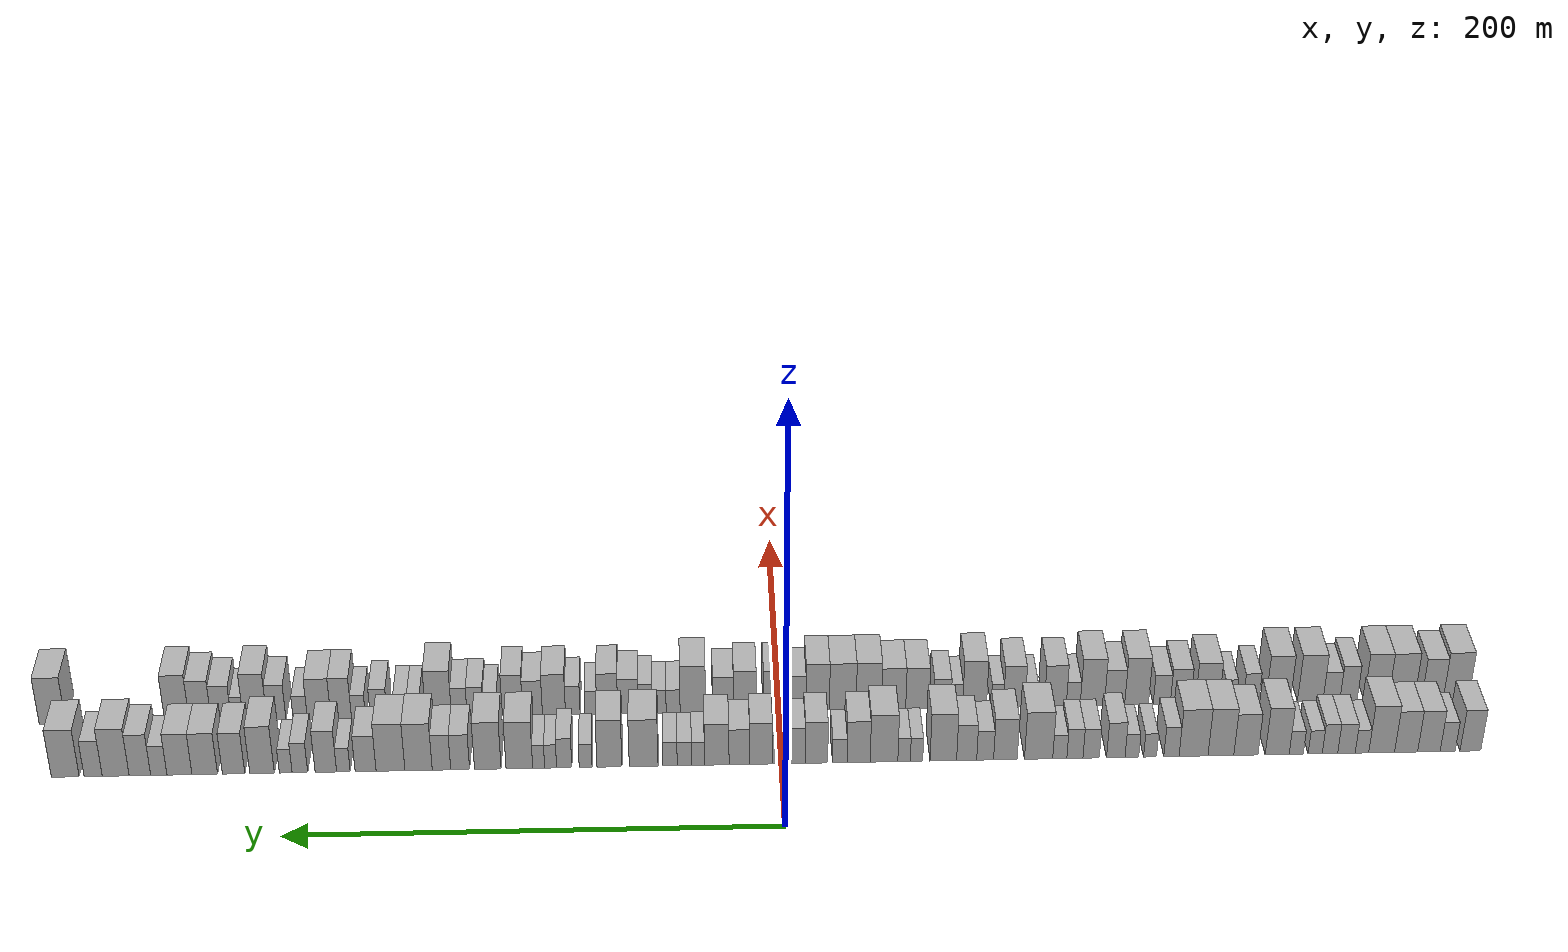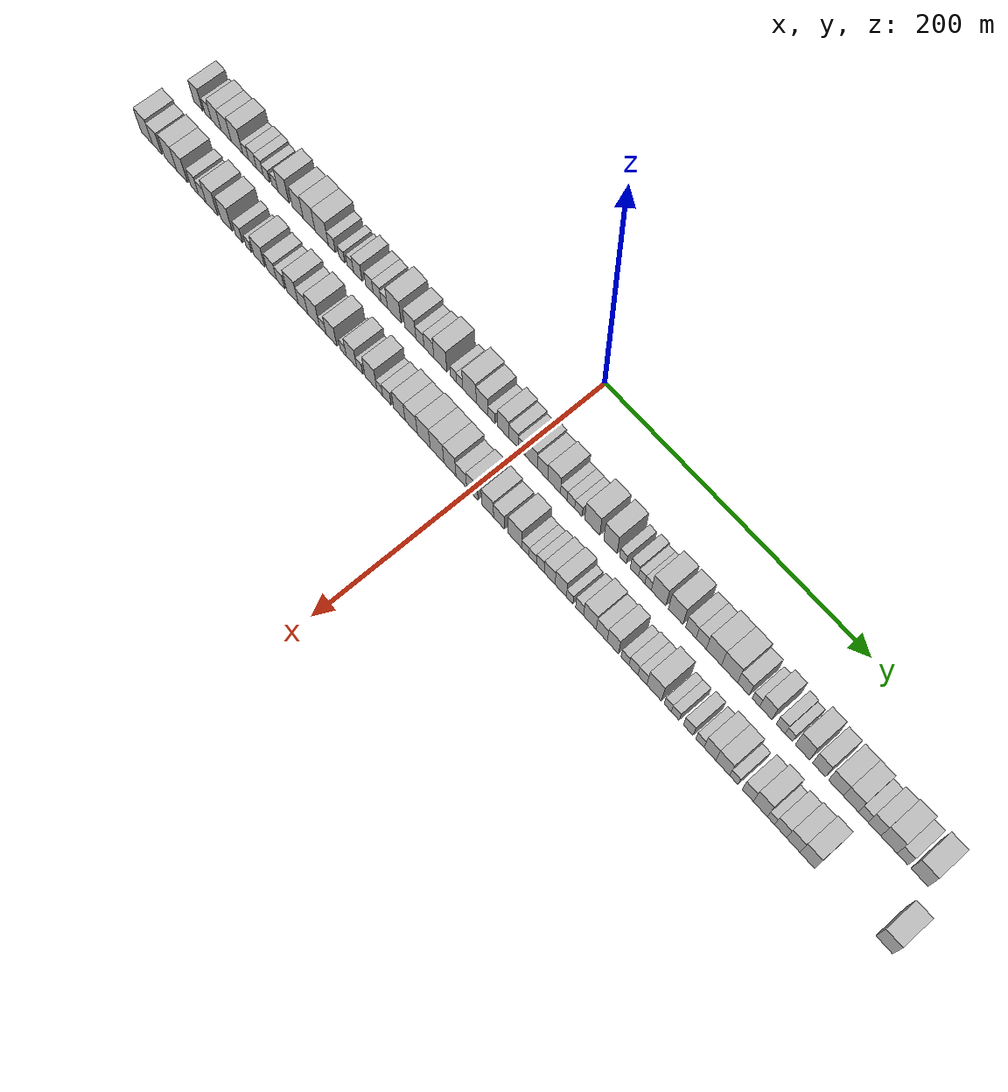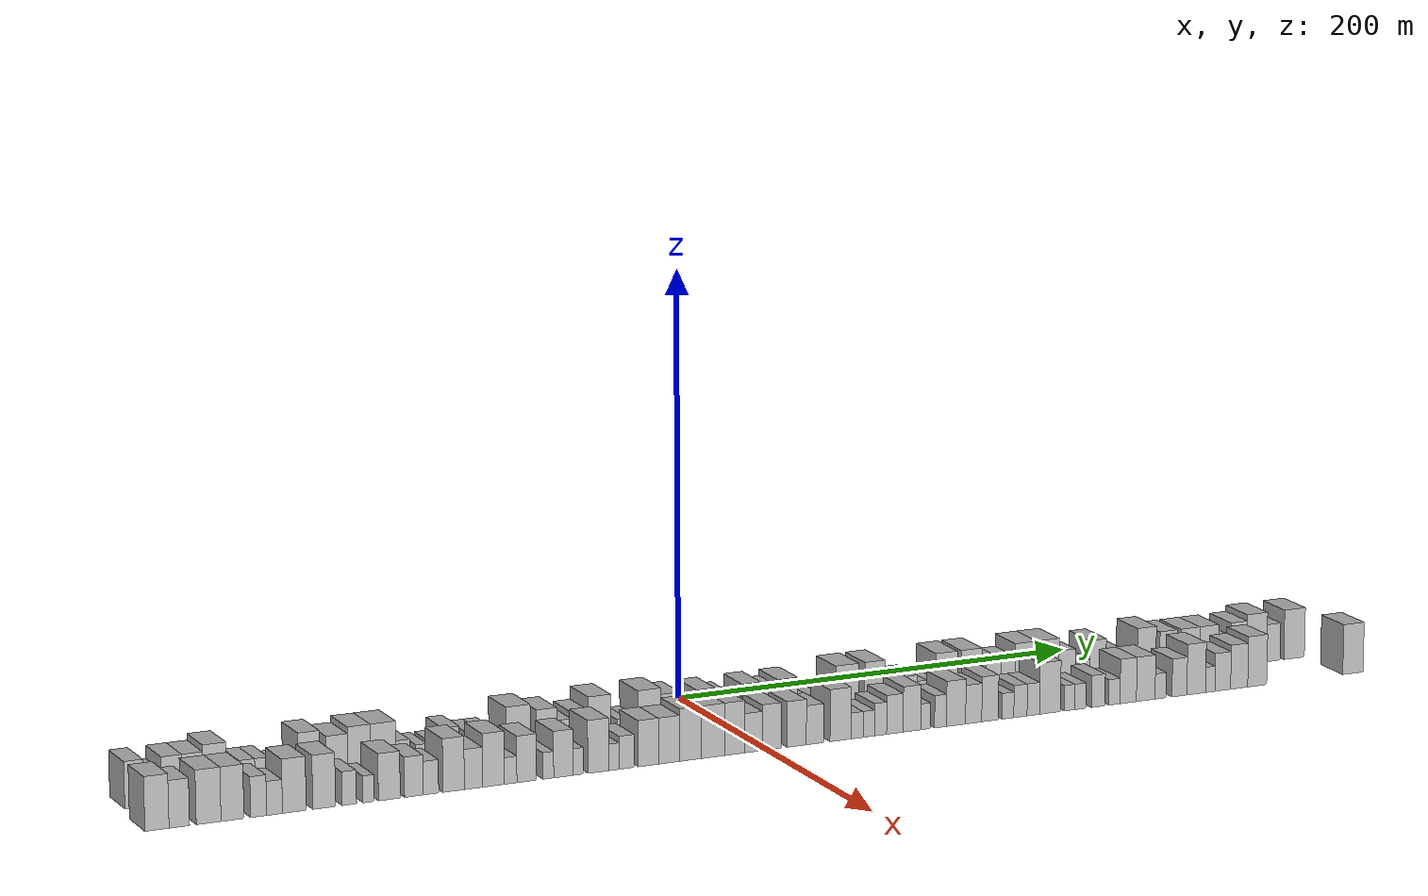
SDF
<sdf version="1.6">
 <world name="default">
  <scene>
   <sky><clouds><speed>12</speed></clouds></sky>
   <ambient>0.4 0.4 0.4 1</ambient>
   <background>0.7 0.7 0.7 1</background>
   <shadows>1</shadows>
  </scene>
  <gravity>0 0 -9.8066</gravity>
  <magnetic_field>6e-06 2.3e-05 -4.2e-05</magnetic_field>
  <physics default="0" name="default_physics" type="ode">
   <ode>
    <solver>
     <type>quick</type>
     <iters>10</iters>
     <sor>1.0</sor>
     <use_dynamic_moi_rescaling>0</use_dynamic_moi_rescaling>
    </solver>
    <constraints>
     <cfm>0</cfm>
     <erp>0.2</erp>
     <contact_max_correcting_vel>100</contact_max_correcting_vel>
     <contact_surface_layer>0.001</contact_surface_layer>
    </constraints>
   </ode>
   <max_step_size>0.004</max_step_size>
   <real_time_factor>1</real_time_factor>
   <real_time_update_rate>250</real_time_update_rate>
  </physics>
  <light name="sun" type="directional">
   <pose>0 0 10 0 0 0</pose>
   <diffuse>0.8 0.8 0.8 1</diffuse>
   <specular>0.2 0.2 0.2 1</specular>
   <attenuation>
    <range>1000</range>
    <constant>0.9</constant>
    <linear>0.01</linear>
    <quadratic>0.001</quadratic>
   </attenuation>
   <direction>-0.5 0.1 -0.9</direction>
  </light>
  <model name="building_1">
   <static>1</static>
   <pose>50.0000 -282.7054 0 0.000000 0.000000 0.000000</pose>
   <link name="link">
    <pose>0 0 10.50 0 0 0</pose>
    <collision name="collision"><geometry><box><size>20.0000 8.5893 21.0000</size></box></geometry></collision>
    <visual name="visual">
     <cast_shadows>0</cast_shadows>
     <geometry><box><size>20.0000 8.5893 21.0000</size></box></geometry>
     <material>
      <script>
       <uri>model://HANNAS_wall/materials/scripts</uri>
       <uri>model://HANNAS_wall/materials/textures</uri>
       <name>vrc/HANNAS_wall</name>
      </script>
     </material>
    </visual>
   </link>
  </model>
  <model name="building_2">
   <static>1</static>
   <pose>50.0000 -273.3137 0 0.000000 0.000000 0.000000</pose>
   <link name="link">
    <pose>0 0 7.50 0 0 0</pose>
    <collision name="collision"><geometry><box><size>20.0000 6.1940 15.0000</size></box></geometry></collision>
    <visual name="visual">
     <cast_shadows>0</cast_shadows>
     <geometry><box><size>20.0000 6.1940 15.0000</size></box></geometry>
     <material>
      <script>
       <uri>model://HANNAS_wall/materials/scripts</uri>
       <uri>model://HANNAS_wall/materials/textures</uri>
       <name>vrc/HANNAS_wall</name>
      </script>
     </material>
    </visual>
   </link>
  </model>
  <model name="building_3">
   <static>1</static>
   <pose>50.0000 -265.5735 0 0.000000 0.000000 0.000000</pose>
   <link name="link">
    <pose>0 0 10.50 0 0 0</pose>
    <collision name="collision"><geometry><box><size>20.0000 9.2864 21.0000</size></box></geometry></collision>
    <visual name="visual">
     <cast_shadows>0</cast_shadows>
     <geometry><box><size>20.0000 9.2864 21.0000</size></box></geometry>
     <material>
      <script>
       <uri>model://HANNAS_wall/materials/scripts</uri>
       <uri>model://HANNAS_wall/materials/textures</uri>
       <name>vrc/HANNAS_wall</name>
      </script>
     </material>
    </visual>
   </link>
  </model>
  <model name="building_4">
   <static>1</static>
   <pose>50.0000 -256.1749 0 0.000000 0.000000 0.000000</pose>
   <link name="link">
    <pose>0 0 10.50 0 0 0</pose>
    <collision name="collision"><geometry><box><size>20.0000 9.5108 21.0000</size></box></geometry></collision>
    <visual name="visual">
     <cast_shadows>0</cast_shadows>
     <geometry><box><size>20.0000 9.5108 21.0000</size></box></geometry>
     <material>
      <script>
       <uri>model://HANNAS_wall/materials/scripts</uri>
       <uri>model://HANNAS_wall/materials/textures</uri>
       <name>vrc/HANNAS_wall</name>
      </script>
     </material>
    </visual>
   </link>
  </model>
  <model name="building_5">
   <static>1</static>
   <pose>50.0000 -246.0718 0 0.000000 0.000000 0.000000</pose>
   <link name="link">
    <pose>0 0 12.00 0 0 0</pose>
    <collision name="collision"><geometry><box><size>20.0000 10.6954 24.0000</size></box></geometry></collision>
    <visual name="visual">
     <cast_shadows>0</cast_shadows>
     <geometry><box><size>20.0000 10.6954 24.0000</size></box></geometry>
     <material>
      <script>
       <uri>model://HANNAS_wall/materials/scripts</uri>
       <uri>model://HANNAS_wall/materials/textures</uri>
       <name>vrc/HANNAS_wall</name>
      </script>
     </material>
    </visual>
   </link>
  </model>
  <model name="building_6">
   <static>1</static>
   <pose>50.0000 -237.9298 0 0.000000 0.000000 0.000000</pose>
   <link name="link">
    <pose>0 0 6.00 0 0 0</pose>
    <collision name="collision"><geometry><box><size>20.0000 5.5887 12.0000</size></box></geometry></collision>
    <visual name="visual">
     <cast_shadows>0</cast_shadows>
     <geometry><box><size>20.0000 5.5887 12.0000</size></box></geometry>
     <material>
      <script>
       <uri>model://HANNAS_wall/materials/scripts</uri>
       <uri>model://HANNAS_wall/materials/textures</uri>
       <name>vrc/HANNAS_wall</name>
      </script>
     </material>
    </visual>
   </link>
  </model>
  <model name="building_7">
   <static>1</static>
   <pose>50.0000 -231.5289 0 0.000000 0.000000 0.000000</pose>
   <link name="link">
    <pose>0 0 7.50 0 0 0</pose>
    <collision name="collision"><geometry><box><size>20.0000 7.2132 15.0000</size></box></geometry></collision>
    <visual name="visual">
     <cast_shadows>0</cast_shadows>
     <geometry><box><size>20.0000 7.2132 15.0000</size></box></geometry>
     <material>
      <script>
       <uri>model://HANNAS_wall/materials/scripts</uri>
       <uri>model://HANNAS_wall/materials/textures</uri>
       <name>vrc/HANNAS_wall</name>
      </script>
     </material>
    </visual>
   </link>
  </model>
  <model name="building_8">
   <static>1</static>
   <pose>50.0000 -224.7328 0 0.000000 0.000000 0.000000</pose>
   <link name="link">
    <pose>0 0 7.50 0 0 0</pose>
    <collision name="collision"><geometry><box><size>20.0000 6.3789 15.0000</size></box></geometry></collision>
    <visual name="visual">
     <cast_shadows>0</cast_shadows>
     <geometry><box><size>20.0000 6.3789 15.0000</size></box></geometry>
     <material>
      <script>
       <uri>model://HANNAS_wall/materials/scripts</uri>
       <uri>model://HANNAS_wall/materials/textures</uri>
       <name>vrc/HANNAS_wall</name>
      </script>
     </material>
    </visual>
   </link>
  </model>
  <model name="building_9">
   <static>1</static>
   <pose>50.0000 -218.6347 0 0.000000 0.000000 0.000000</pose>
   <link name="link">
    <pose>0 0 6.00 0 0 0</pose>
    <collision name="collision"><geometry><box><size>20.0000 5.8174 12.0000</size></box></geometry></collision>
    <visual name="visual">
     <cast_shadows>0</cast_shadows>
     <geometry><box><size>20.0000 5.8174 12.0000</size></box></geometry>
     <material>
      <script>
       <uri>model://HANNAS_wall/materials/scripts</uri>
       <uri>model://HANNAS_wall/materials/textures</uri>
       <name>vrc/HANNAS_wall</name>
      </script>
     </material>
    </visual>
   </link>
  </model>
  <model name="building_10">
   <static>1</static>
   <pose>50.0000 -210.8293 0 0.000000 0.000000 0.000000</pose>
   <link name="link">
    <pose>0 0 6.00 0 0 0</pose>
    <collision name="collision"><geometry><box><size>20.0000 5.7934 12.0000</size></box></geometry></collision>
    <visual name="visual">
     <cast_shadows>0</cast_shadows>
     <geometry><box><size>20.0000 5.7934 12.0000</size></box></geometry>
     <material>
      <script>
       <uri>model://HANNAS_wall/materials/scripts</uri>
       <uri>model://HANNAS_wall/materials/textures</uri>
       <name>vrc/HANNAS_wall</name>
      </script>
     </material>
    </visual>
   </link>
  </model>
  <model name="building_11">
   <static>1</static>
   <pose>50.0000 -202.9933 0 0.000000 0.000000 0.000000</pose>
   <link name="link">
    <pose>0 0 12.00 0 0 0</pose>
    <collision name="collision"><geometry><box><size>20.0000 9.8786 24.0000</size></box></geometry></collision>
    <visual name="visual">
     <cast_shadows>0</cast_shadows>
     <geometry><box><size>20.0000 9.8786 24.0000</size></box></geometry>
     <material>
      <script>
       <uri>model://HANNAS_wall/materials/scripts</uri>
       <uri>model://HANNAS_wall/materials/textures</uri>
       <name>vrc/HANNAS_wall</name>
      </script>
     </material>
    </visual>
   </link>
  </model>
  <model name="building_12">
   <static>1</static>
   <pose>50.0000 -190.0922 0 0.000000 0.000000 0.000000</pose>
   <link name="link">
    <pose>0 0 10.50 0 0 0</pose>
    <collision name="collision"><geometry><box><size>20.0000 9.9234 21.0000</size></box></geometry></collision>
    <visual name="visual">
     <cast_shadows>0</cast_shadows>
     <geometry><box><size>20.0000 9.9234 21.0000</size></box></geometry>
     <material>
      <script>
       <uri>model://HANNAS_wall/materials/scripts</uri>
       <uri>model://HANNAS_wall/materials/textures</uri>
       <name>vrc/HANNAS_wall</name>
      </script>
     </material>
    </visual>
   </link>
  </model>
  <model name="building_13">
   <static>1</static>
   <pose>50.0000 -179.8102 0 0.000000 0.000000 0.000000</pose>
   <link name="link">
    <pose>0 0 12.00 0 0 0</pose>
    <collision name="collision"><geometry><box><size>20.0000 10.6407 24.0000</size></box></geometry></collision>
    <visual name="visual">
     <cast_shadows>0</cast_shadows>
     <geometry><box><size>20.0000 10.6407 24.0000</size></box></geometry>
     <material>
      <script>
       <uri>model://HANNAS_wall/materials/scripts</uri>
       <uri>model://HANNAS_wall/materials/textures</uri>
       <name>vrc/HANNAS_wall</name>
      </script>
     </material>
    </visual>
   </link>
  </model>
  <model name="building_14">
   <static>1</static>
   <pose>50.0000 -168.5287 0 0.000000 0.000000 0.000000</pose>
   <link name="link">
    <pose>0 0 12.00 0 0 0</pose>
    <collision name="collision"><geometry><box><size>20.0000 11.9223 24.0000</size></box></geometry></collision>
    <visual name="visual">
     <cast_shadows>0</cast_shadows>
     <geometry><box><size>20.0000 11.9223 24.0000</size></box></geometry>
     <material>
      <script>
       <uri>model://HANNAS_wall/materials/scripts</uri>
       <uri>model://HANNAS_wall/materials/textures</uri>
       <name>vrc/HANNAS_wall</name>
      </script>
     </material>
    </visual>
   </link>
  </model>
  <model name="building_15">
   <static>1</static>
   <pose>50.0000 -159.4381 0 0.000000 0.000000 0.000000</pose>
   <link name="link">
    <pose>0 0 7.50 0 0 0</pose>
    <collision name="collision"><geometry><box><size>20.0000 6.2589 15.0000</size></box></geometry></collision>
    <visual name="visual">
     <cast_shadows>0</cast_shadows>
     <geometry><box><size>20.0000 6.2589 15.0000</size></box></geometry>
     <material>
      <script>
       <uri>model://HANNAS_wall/materials/scripts</uri>
       <uri>model://HANNAS_wall/materials/textures</uri>
       <name>vrc/HANNAS_wall</name>
      </script>
     </material>
    </visual>
   </link>
  </model>
  <model name="building_16">
   <static>1</static>
   <pose>50.0000 -150.6454 0 0.000000 0.000000 0.000000</pose>
   <link name="link">
    <pose>0 0 6.00 0 0 0</pose>
    <collision name="collision"><geometry><box><size>20.0000 5.3266 12.0000</size></box></geometry></collision>
    <visual name="visual">
     <cast_shadows>0</cast_shadows>
     <geometry><box><size>20.0000 5.3266 12.0000</size></box></geometry>
     <material>
      <script>
       <uri>model://HANNAS_wall/materials/scripts</uri>
       <uri>model://HANNAS_wall/materials/textures</uri>
       <name>vrc/HANNAS_wall</name>
      </script>
     </material>
    </visual>
   </link>
  </model>
  <model name="building_17">
   <static>1</static>
   <pose>50.0000 -143.1779 0 0.000000 0.000000 0.000000</pose>
   <link name="link">
    <pose>0 0 6.00 0 0 0</pose>
    <collision name="collision"><geometry><box><size>20.0000 5.6084 12.0000</size></box></geometry></collision>
    <visual name="visual">
     <cast_shadows>0</cast_shadows>
     <geometry><box><size>20.0000 5.6084 12.0000</size></box></geometry>
     <material>
      <script>
       <uri>model://HANNAS_wall/materials/scripts</uri>
       <uri>model://HANNAS_wall/materials/textures</uri>
       <name>vrc/HANNAS_wall</name>
      </script>
     </material>
    </visual>
   </link>
  </model>
  <model name="building_18">
   <static>1</static>
   <pose>50.0000 -136.5810 0 0.000000 0.000000 0.000000</pose>
   <link name="link">
    <pose>0 0 9.00 0 0 0</pose>
    <collision name="collision"><geometry><box><size>20.0000 7.5854 18.0000</size></box></geometry></collision>
    <visual name="visual">
     <cast_shadows>0</cast_shadows>
     <geometry><box><size>20.0000 7.5854 18.0000</size></box></geometry>
     <material>
      <script>
       <uri>model://HANNAS_wall/materials/scripts</uri>
       <uri>model://HANNAS_wall/materials/textures</uri>
       <name>vrc/HANNAS_wall</name>
      </script>
     </material>
    </visual>
   </link>
  </model>
  <model name="building_19">
   <static>1</static>
   <pose>50.0000 -126.4418 0 0.000000 0.000000 0.000000</pose>
   <link name="link">
    <pose>0 0 7.50 0 0 0</pose>
    <collision name="collision"><geometry><box><size>20.0000 6.6930 15.0000</size></box></geometry></collision>
    <visual name="visual">
     <cast_shadows>0</cast_shadows>
     <geometry><box><size>20.0000 6.6930 15.0000</size></box></geometry>
     <material>
      <script>
       <uri>model://HANNAS_wall/materials/scripts</uri>
       <uri>model://HANNAS_wall/materials/textures</uri>
       <name>vrc/HANNAS_wall</name>
      </script>
     </material>
    </visual>
   </link>
  </model>
  <model name="building_20">
   <static>1</static>
   <pose>50.0000 -119.7794 0 0.000000 0.000000 0.000000</pose>
   <link name="link">
    <pose>0 0 7.50 0 0 0</pose>
    <collision name="collision"><geometry><box><size>20.0000 6.6319 15.0000</size></box></geometry></collision>
    <visual name="visual">
     <cast_shadows>0</cast_shadows>
     <geometry><box><size>20.0000 6.6319 15.0000</size></box></geometry>
     <material>
      <script>
       <uri>model://HANNAS_wall/materials/scripts</uri>
       <uri>model://HANNAS_wall/materials/textures</uri>
       <name>vrc/HANNAS_wall</name>
      </script>
     </material>
    </visual>
   </link>
  </model>
  <model name="building_21">
   <static>1</static>
   <pose>50.0000 -113.5627 0 0.000000 0.000000 0.000000</pose>
   <link name="link">
    <pose>0 0 6.00 0 0 0</pose>
    <collision name="collision"><geometry><box><size>20.0000 5.8016 12.0000</size></box></geometry></collision>
    <visual name="visual">
     <cast_shadows>0</cast_shadows>
     <geometry><box><size>20.0000 5.8016 12.0000</size></box></geometry>
     <material>
      <script>
       <uri>model://HANNAS_wall/materials/scripts</uri>
       <uri>model://HANNAS_wall/materials/textures</uri>
       <name>vrc/HANNAS_wall</name>
      </script>
     </material>
    </visual>
   </link>
  </model>
  <model name="building_22">
   <static>1</static>
   <pose>50.0000 -104.8681 0 0.000000 0.000000 0.000000</pose>
   <link name="link">
    <pose>0 0 12.00 0 0 0</pose>
    <collision name="collision"><geometry><box><size>20.0000 11.5875 24.0000</size></box></geometry></collision>
    <visual name="visual">
     <cast_shadows>0</cast_shadows>
     <geometry><box><size>20.0000 11.5875 24.0000</size></box></geometry>
     <material>
      <script>
       <uri>model://HANNAS_wall/materials/scripts</uri>
       <uri>model://HANNAS_wall/materials/textures</uri>
       <name>vrc/HANNAS_wall</name>
      </script>
     </material>
    </visual>
   </link>
  </model>
  <model name="building_23">
   <static>1</static>
   <pose>50.0000 -91.2402 0 0.000000 0.000000 0.000000</pose>
   <link name="link">
    <pose>0 0 10.50 0 0 0</pose>
    <collision name="collision"><geometry><box><size>20.0000 9.6684 21.0000</size></box></geometry></collision>
    <visual name="visual">
     <cast_shadows>0</cast_shadows>
     <geometry><box><size>20.0000 9.6684 21.0000</size></box></geometry>
     <material>
      <script>
       <uri>model://HANNAS_wall/materials/scripts</uri>
       <uri>model://HANNAS_wall/materials/textures</uri>
       <name>vrc/HANNAS_wall</name>
      </script>
     </material>
    </visual>
   </link>
  </model>
  <model name="building_24">
   <static>1</static>
   <pose>50.0000 -82.9417 0 0.000000 0.000000 0.000000</pose>
   <link name="link">
    <pose>0 0 7.50 0 0 0</pose>
    <collision name="collision"><geometry><box><size>20.0000 6.9285 15.0000</size></box></geometry></collision>
    <visual name="visual">
     <cast_shadows>0</cast_shadows>
     <geometry><box><size>20.0000 6.9285 15.0000</size></box></geometry>
     <material>
      <script>
       <uri>model://HANNAS_wall/materials/scripts</uri>
       <uri>model://HANNAS_wall/materials/textures</uri>
       <name>vrc/HANNAS_wall</name>
      </script>
     </material>
    </visual>
   </link>
  </model>
  <model name="building_25">
   <static>1</static>
   <pose>50.0000 -75.3658 0 0.000000 0.000000 0.000000</pose>
   <link name="link">
    <pose>0 0 9.00 0 0 0</pose>
    <collision name="collision"><geometry><box><size>20.0000 8.2234 18.0000</size></box></geometry></collision>
    <visual name="visual">
     <cast_shadows>0</cast_shadows>
     <geometry><box><size>20.0000 8.2234 18.0000</size></box></geometry>
     <material>
      <script>
       <uri>model://HANNAS_wall/materials/scripts</uri>
       <uri>model://HANNAS_wall/materials/textures</uri>
       <name>vrc/HANNAS_wall</name>
      </script>
     </material>
    </visual>
   </link>
  </model>
  <model name="building_26">
   <static>1</static>
   <pose>50.0000 -65.8035 0 0.000000 0.000000 0.000000</pose>
   <link name="link">
    <pose>0 0 12.00 0 0 0</pose>
    <collision name="collision"><geometry><box><size>20.0000 10.9014 24.0000</size></box></geometry></collision>
    <visual name="visual">
     <cast_shadows>0</cast_shadows>
     <geometry><box><size>20.0000 10.9014 24.0000</size></box></geometry>
     <material>
      <script>
       <uri>model://HANNAS_wall/materials/scripts</uri>
       <uri>model://HANNAS_wall/materials/textures</uri>
       <name>vrc/HANNAS_wall</name>
      </script>
     </material>
    </visual>
   </link>
  </model>
  <model name="building_27">
   <static>1</static>
   <pose>50.0000 -54.8230 0 0.000000 0.000000 0.000000</pose>
   <link name="link">
    <pose>0 0 6.00 0 0 0</pose>
    <collision name="collision"><geometry><box><size>20.0000 5.0596 12.0000</size></box></geometry></collision>
    <visual name="visual">
     <cast_shadows>0</cast_shadows>
     <geometry><box><size>20.0000 5.0596 12.0000</size></box></geometry>
     <material>
      <script>
       <uri>model://HANNAS_wall/materials/scripts</uri>
       <uri>model://HANNAS_wall/materials/textures</uri>
       <name>vrc/HANNAS_wall</name>
      </script>
     </material>
    </visual>
   </link>
  </model>
  <model name="building_28">
   <static>1</static>
   <pose>50.0000 -49.7295 0 0.000000 0.000000 0.000000</pose>
   <link name="link">
    <pose>0 0 6.00 0 0 0</pose>
    <collision name="collision"><geometry><box><size>20.0000 5.1273 12.0000</size></box></geometry></collision>
    <visual name="visual">
     <cast_shadows>0</cast_shadows>
     <geometry><box><size>20.0000 5.1273 12.0000</size></box></geometry>
     <material>
      <script>
       <uri>model://HANNAS_wall/materials/scripts</uri>
       <uri>model://HANNAS_wall/materials/textures</uri>
       <name>vrc/HANNAS_wall</name>
      </script>
     </material>
    </visual>
   </link>
  </model>
  <model name="building_29">
   <static>1</static>
   <pose>50.0000 -41.5138 0 0.000000 0.000000 0.000000</pose>
   <link name="link">
    <pose>0 0 12.00 0 0 0</pose>
    <collision name="collision"><geometry><box><size>20.0000 11.3039 24.0000</size></box></geometry></collision>
    <visual name="visual">
     <cast_shadows>0</cast_shadows>
     <geometry><box><size>20.0000 11.3039 24.0000</size></box></geometry>
     <material>
      <script>
       <uri>model://HANNAS_wall/materials/scripts</uri>
       <uri>model://HANNAS_wall/materials/textures</uri>
       <name>vrc/HANNAS_wall</name>
      </script>
     </material>
    </visual>
   </link>
  </model>
  <model name="building_30">
   <static>1</static>
   <pose>50.0000 -31.1243 0 0.000000 0.000000 0.000000</pose>
   <link name="link">
    <pose>0 0 10.50 0 0 0</pose>
    <collision name="collision"><geometry><box><size>20.0000 9.4751 21.0000</size></box></geometry></collision>
    <visual name="visual">
     <cast_shadows>0</cast_shadows>
     <geometry><box><size>20.0000 9.4751 21.0000</size></box></geometry>
     <material>
      <script>
       <uri>model://HANNAS_wall/materials/scripts</uri>
       <uri>model://HANNAS_wall/materials/textures</uri>
       <name>vrc/HANNAS_wall</name>
      </script>
     </material>
    </visual>
   </link>
  </model>
  <model name="building_31">
   <static>1</static>
   <pose>50.0000 -23.4259 0 0.000000 0.000000 0.000000</pose>
   <link name="link">
    <pose>0 0 6.00 0 0 0</pose>
    <collision name="collision"><geometry><box><size>20.0000 5.9219 12.0000</size></box></geometry></collision>
    <visual name="visual">
     <cast_shadows>0</cast_shadows>
     <geometry><box><size>20.0000 5.9219 12.0000</size></box></geometry>
     <material>
      <script>
       <uri>model://HANNAS_wall/materials/scripts</uri>
       <uri>model://HANNAS_wall/materials/textures</uri>
       <name>vrc/HANNAS_wall</name>
      </script>
     </material>
    </visual>
   </link>
  </model>
  <model name="building_32">
   <static>1</static>
   <pose>50.0000 -13.8963 0 0.000000 0.000000 0.000000</pose>
   <link name="link">
    <pose>0 0 10.50 0 0 0</pose>
    <collision name="collision"><geometry><box><size>20.0000 9.1371 21.0000</size></box></geometry></collision>
    <visual name="visual">
     <cast_shadows>0</cast_shadows>
     <geometry><box><size>20.0000 9.1371 21.0000</size></box></geometry>
     <material>
      <script>
       <uri>model://HANNAS_wall/materials/scripts</uri>
       <uri>model://HANNAS_wall/materials/textures</uri>
       <name>vrc/HANNAS_wall</name>
      </script>
     </material>
    </visual>
   </link>
  </model>
  <model name="building_33">
   <static>1</static>
   <pose>50.0000 -5.6347 0 0.000000 0.000000 0.000000</pose>
   <link name="link">
    <pose>0 0 9.00 0 0 0</pose>
    <collision name="collision"><geometry><box><size>20.0000 7.3862 18.0000</size></box></geometry></collision>
    <visual name="visual">
     <cast_shadows>0</cast_shadows>
     <geometry><box><size>20.0000 7.3862 18.0000</size></box></geometry>
     <material>
      <script>
       <uri>model://HANNAS_wall/materials/scripts</uri>
       <uri>model://HANNAS_wall/materials/textures</uri>
       <name>vrc/HANNAS_wall</name>
      </script>
     </material>
    </visual>
   </link>
  </model>
  <model name="building_34">
   <static>1</static>
   <pose>50.0000 1.0851 0 0.000000 0.000000 0.000000</pose>
   <link name="link">
    <pose>0 0 7.50 0 0 0</pose>
    <collision name="collision"><geometry><box><size>20.0000 6.0533 15.0000</size></box></geometry></collision>
    <visual name="visual">
     <cast_shadows>0</cast_shadows>
     <geometry><box><size>20.0000 6.0533 15.0000</size></box></geometry>
     <material>
      <script>
       <uri>model://HANNAS_wall/materials/scripts</uri>
       <uri>model://HANNAS_wall/materials/textures</uri>
       <name>vrc/HANNAS_wall</name>
      </script>
     </material>
    </visual>
   </link>
  </model>
  <model name="building_35">
   <static>1</static>
   <pose>50.0000 8.7507 0 0.000000 0.000000 0.000000</pose>
   <link name="link">
    <pose>0 0 10.50 0 0 0</pose>
    <collision name="collision"><geometry><box><size>20.0000 9.2780 21.0000</size></box></geometry></collision>
    <visual name="visual">
     <cast_shadows>0</cast_shadows>
     <geometry><box><size>20.0000 9.2780 21.0000</size></box></geometry>
     <material>
      <script>
       <uri>model://HANNAS_wall/materials/scripts</uri>
       <uri>model://HANNAS_wall/materials/textures</uri>
       <name>vrc/HANNAS_wall</name>
      </script>
     </material>
    </visual>
   </link>
  </model>
  <model name="building_36">
   <static>1</static>
   <pose>50.0000 17.6079 0 0.000000 0.000000 0.000000</pose>
   <link name="link">
    <pose>0 0 9.00 0 0 0</pose>
    <collision name="collision"><geometry><box><size>20.0000 8.4364 18.0000</size></box></geometry></collision>
    <visual name="visual">
     <cast_shadows>0</cast_shadows>
     <geometry><box><size>20.0000 8.4364 18.0000</size></box></geometry>
     <material>
      <script>
       <uri>model://HANNAS_wall/materials/scripts</uri>
       <uri>model://HANNAS_wall/materials/textures</uri>
       <name>vrc/HANNAS_wall</name>
      </script>
     </material>
    </visual>
   </link>
  </model>
  <model name="building_37">
   <static>1</static>
   <pose>50.0000 26.8337 0 0.000000 0.000000 0.000000</pose>
   <link name="link">
    <pose>0 0 10.50 0 0 0</pose>
    <collision name="collision"><geometry><box><size>20.0000 10.0153 21.0000</size></box></geometry></collision>
    <visual name="visual">
     <cast_shadows>0</cast_shadows>
     <geometry><box><size>20.0000 10.0153 21.0000</size></box></geometry>
     <material>
      <script>
       <uri>model://HANNAS_wall/materials/scripts</uri>
       <uri>model://HANNAS_wall/materials/textures</uri>
       <name>vrc/HANNAS_wall</name>
      </script>
     </material>
    </visual>
   </link>
  </model>
  <model name="building_38">
   <static>1</static>
   <pose>50.0000 34.4744 0 0.000000 0.000000 0.000000</pose>
   <link name="link">
    <pose>0 0 6.00 0 0 0</pose>
    <collision name="collision"><geometry><box><size>20.0000 5.2660 12.0000</size></box></geometry></collision>
    <visual name="visual">
     <cast_shadows>0</cast_shadows>
     <geometry><box><size>20.0000 5.2660 12.0000</size></box></geometry>
     <material>
      <script>
       <uri>model://HANNAS_wall/materials/scripts</uri>
       <uri>model://HANNAS_wall/materials/textures</uri>
       <name>vrc/HANNAS_wall</name>
      </script>
     </material>
    </visual>
   </link>
  </model>
  <model name="building_39">
   <static>1</static>
   <pose>50.0000 40.0444 0 0.000000 0.000000 0.000000</pose>
   <link name="link">
    <pose>0 0 6.00 0 0 0</pose>
    <collision name="collision"><geometry><box><size>20.0000 5.8741 12.0000</size></box></geometry></collision>
    <visual name="visual">
     <cast_shadows>0</cast_shadows>
     <geometry><box><size>20.0000 5.8741 12.0000</size></box></geometry>
     <material>
      <script>
       <uri>model://HANNAS_wall/materials/scripts</uri>
       <uri>model://HANNAS_wall/materials/textures</uri>
       <name>vrc/HANNAS_wall</name>
      </script>
     </material>
    </visual>
   </link>
  </model>
  <model name="building_40">
   <static>1</static>
   <pose>50.0000 45.8900 0 0.000000 0.000000 0.000000</pose>
   <link name="link">
    <pose>0 0 6.00 0 0 0</pose>
    <collision name="collision"><geometry><box><size>20.0000 5.8171 12.0000</size></box></geometry></collision>
    <visual name="visual">
     <cast_shadows>0</cast_shadows>
     <geometry><box><size>20.0000 5.8171 12.0000</size></box></geometry>
     <material>
      <script>
       <uri>model://HANNAS_wall/materials/scripts</uri>
       <uri>model://HANNAS_wall/materials/textures</uri>
       <name>vrc/HANNAS_wall</name>
      </script>
     </material>
    </visual>
   </link>
  </model>
  <model name="building_41">
   <static>1</static>
   <pose>50.0000 56.6589 0 0.000000 0.000000 0.000000</pose>
   <link name="link">
    <pose>0 0 12.00 0 0 0</pose>
    <collision name="collision"><geometry><box><size>20.0000 11.7206 24.0000</size></box></geometry></collision>
    <visual name="visual">
     <cast_shadows>0</cast_shadows>
     <geometry><box><size>20.0000 11.7206 24.0000</size></box></geometry>
     <material>
      <script>
       <uri>model://HANNAS_wall/materials/scripts</uri>
       <uri>model://HANNAS_wall/materials/textures</uri>
       <name>vrc/HANNAS_wall</name>
      </script>
     </material>
    </visual>
   </link>
  </model>
  <model name="building_42">
   <static>1</static>
   <pose>50.0000 70.6065 0 0.000000 0.000000 0.000000</pose>
   <link name="link">
    <pose>0 0 12.00 0 0 0</pose>
    <collision name="collision"><geometry><box><size>20.0000 10.1746 24.0000</size></box></geometry></collision>
    <visual name="visual">
     <cast_shadows>0</cast_shadows>
     <geometry><box><size>20.0000 10.1746 24.0000</size></box></geometry>
     <material>
      <script>
       <uri>model://HANNAS_wall/materials/scripts</uri>
       <uri>model://HANNAS_wall/materials/textures</uri>
       <name>vrc/HANNAS_wall</name>
      </script>
     </material>
    </visual>
   </link>
  </model>
  <model name="building_43">
   <static>1</static>
   <pose>50.0000 80.3176 0 0.000000 0.000000 0.000000</pose>
   <link name="link">
    <pose>0 0 6.00 0 0 0</pose>
    <collision name="collision"><geometry><box><size>20.0000 5.2476 12.0000</size></box></geometry></collision>
    <visual name="visual">
     <cast_shadows>0</cast_shadows>
     <geometry><box><size>20.0000 5.2476 12.0000</size></box></geometry>
     <material>
      <script>
       <uri>model://HANNAS_wall/materials/scripts</uri>
       <uri>model://HANNAS_wall/materials/textures</uri>
       <name>vrc/HANNAS_wall</name>
      </script>
     </material>
    </visual>
   </link>
  </model>
  <model name="building_44">
   <static>1</static>
   <pose>50.0000 89.0435 0 0.000000 0.000000 0.000000</pose>
   <link name="link">
    <pose>0 0 7.50 0 0 0</pose>
    <collision name="collision"><geometry><box><size>20.0000 6.2043 15.0000</size></box></geometry></collision>
    <visual name="visual">
     <cast_shadows>0</cast_shadows>
     <geometry><box><size>20.0000 6.2043 15.0000</size></box></geometry>
     <material>
      <script>
       <uri>model://HANNAS_wall/materials/scripts</uri>
       <uri>model://HANNAS_wall/materials/textures</uri>
       <name>vrc/HANNAS_wall</name>
      </script>
     </material>
    </visual>
   </link>
  </model>
  <model name="building_45">
   <static>1</static>
   <pose>50.0000 94.5717 0 0.000000 0.000000 0.000000</pose>
   <link name="link">
    <pose>0 0 6.00 0 0 0</pose>
    <collision name="collision"><geometry><box><size>20.0000 4.8520 12.0000</size></box></geometry></collision>
    <visual name="visual">
     <cast_shadows>0</cast_shadows>
     <geometry><box><size>20.0000 4.8520 12.0000</size></box></geometry>
     <material>
      <script>
       <uri>model://HANNAS_wall/materials/scripts</uri>
       <uri>model://HANNAS_wall/materials/textures</uri>
       <name>vrc/HANNAS_wall</name>
      </script>
     </material>
    </visual>
   </link>
  </model>
  <model name="building_46">
   <static>1</static>
   <pose>50.0000 99.4362 0 0.000000 0.000000 0.000000</pose>
   <link name="link">
    <pose>0 0 6.00 0 0 0</pose>
    <collision name="collision"><geometry><box><size>20.0000 4.8771 12.0000</size></box></geometry></collision>
    <visual name="visual">
     <cast_shadows>0</cast_shadows>
     <geometry><box><size>20.0000 4.8771 12.0000</size></box></geometry>
     <material>
      <script>
       <uri>model://HANNAS_wall/materials/scripts</uri>
       <uri>model://HANNAS_wall/materials/textures</uri>
       <name>vrc/HANNAS_wall</name>
      </script>
     </material>
    </visual>
   </link>
  </model>
  <model name="building_47">
   <static>1</static>
   <pose>50.0000 107.2916 0 0.000000 0.000000 0.000000</pose>
   <link name="link">
    <pose>0 0 12.00 0 0 0</pose>
    <collision name="collision"><geometry><box><size>20.0000 10.8336 24.0000</size></box></geometry></collision>
    <visual name="visual">
     <cast_shadows>0</cast_shadows>
     <geometry><box><size>20.0000 10.8336 24.0000</size></box></geometry>
     <material>
      <script>
       <uri>model://HANNAS_wall/materials/scripts</uri>
       <uri>model://HANNAS_wall/materials/textures</uri>
       <name>vrc/HANNAS_wall</name>
      </script>
     </material>
    </visual>
   </link>
  </model>
  <model name="building_48">
   <static>1</static>
   <pose>50.0000 120.1184 0 0.000000 0.000000 0.000000</pose>
   <link name="link">
    <pose>0 0 12.00 0 0 0</pose>
    <collision name="collision"><geometry><box><size>20.0000 10.8199 24.0000</size></box></geometry></collision>
    <visual name="visual">
     <cast_shadows>0</cast_shadows>
     <geometry><box><size>20.0000 10.8199 24.0000</size></box></geometry>
     <material>
      <script>
       <uri>model://HANNAS_wall/materials/scripts</uri>
       <uri>model://HANNAS_wall/materials/textures</uri>
       <name>vrc/HANNAS_wall</name>
      </script>
     </material>
    </visual>
   </link>
  </model>
  <model name="building_49">
   <static>1</static>
   <pose>50.0000 131.3602 0 0.000000 0.000000 0.000000</pose>
   <link name="link">
    <pose>0 0 9.00 0 0 0</pose>
    <collision name="collision"><geometry><box><size>20.0000 7.6637 18.0000</size></box></geometry></collision>
    <visual name="visual">
     <cast_shadows>0</cast_shadows>
     <geometry><box><size>20.0000 7.6637 18.0000</size></box></geometry>
     <material>
      <script>
       <uri>model://HANNAS_wall/materials/scripts</uri>
       <uri>model://HANNAS_wall/materials/textures</uri>
       <name>vrc/HANNAS_wall</name>
      </script>
     </material>
    </visual>
   </link>
  </model>
  <model name="building_50">
   <static>1</static>
   <pose>50.0000 138.9554 0 0.000000 0.000000 0.000000</pose>
   <link name="link">
    <pose>0 0 9.00 0 0 0</pose>
    <collision name="collision"><geometry><box><size>20.0000 7.5268 18.0000</size></box></geometry></collision>
    <visual name="visual">
     <cast_shadows>0</cast_shadows>
     <geometry><box><size>20.0000 7.5268 18.0000</size></box></geometry>
     <material>
      <script>
       <uri>model://HANNAS_wall/materials/scripts</uri>
       <uri>model://HANNAS_wall/materials/textures</uri>
       <name>vrc/HANNAS_wall</name>
      </script>
     </material>
    </visual>
   </link>
  </model>
  <model name="building_51">
   <static>1</static>
   <pose>50.0000 148.2632 0 0.000000 0.000000 0.000000</pose>
   <link name="link">
    <pose>0 0 12.00 0 0 0</pose>
    <collision name="collision"><geometry><box><size>20.0000 11.0887 24.0000</size></box></geometry></collision>
    <visual name="visual">
     <cast_shadows>0</cast_shadows>
     <geometry><box><size>20.0000 11.0887 24.0000</size></box></geometry>
     <material>
      <script>
       <uri>model://HANNAS_wall/materials/scripts</uri>
       <uri>model://HANNAS_wall/materials/textures</uri>
       <name>vrc/HANNAS_wall</name>
      </script>
     </material>
    </visual>
   </link>
  </model>
  <model name="building_52">
   <static>1</static>
   <pose>50.0000 159.6565 0 0.000000 0.000000 0.000000</pose>
   <link name="link">
    <pose>0 0 12.00 0 0 0</pose>
    <collision name="collision"><geometry><box><size>20.0000 11.6979 24.0000</size></box></geometry></collision>
    <visual name="visual">
     <cast_shadows>0</cast_shadows>
     <geometry><box><size>20.0000 11.6979 24.0000</size></box></geometry>
     <material>
      <script>
       <uri>model://HANNAS_wall/materials/scripts</uri>
       <uri>model://HANNAS_wall/materials/textures</uri>
       <name>vrc/HANNAS_wall</name>
      </script>
     </material>
    </visual>
   </link>
  </model>
  <model name="building_53">
   <static>1</static>
   <pose>50.0000 169.7641 0 0.000000 0.000000 0.000000</pose>
   <link name="link">
    <pose>0 0 9.00 0 0 0</pose>
    <collision name="collision"><geometry><box><size>20.0000 8.5172 18.0000</size></box></geometry></collision>
    <visual name="visual">
     <cast_shadows>0</cast_shadows>
     <geometry><box><size>20.0000 8.5172 18.0000</size></box></geometry>
     <material>
      <script>
       <uri>model://HANNAS_wall/materials/scripts</uri>
       <uri>model://HANNAS_wall/materials/textures</uri>
       <name>vrc/HANNAS_wall</name>
      </script>
     </material>
    </visual>
   </link>
  </model>
  <model name="building_54">
   <static>1</static>
   <pose>50.0000 178.7711 0 0.000000 0.000000 0.000000</pose>
   <link name="link">
    <pose>0 0 6.00 0 0 0</pose>
    <collision name="collision"><geometry><box><size>20.0000 5.4969 12.0000</size></box></geometry></collision>
    <visual name="visual">
     <cast_shadows>0</cast_shadows>
     <geometry><box><size>20.0000 5.4969 12.0000</size></box></geometry>
     <material>
      <script>
       <uri>model://HANNAS_wall/materials/scripts</uri>
       <uri>model://HANNAS_wall/materials/textures</uri>
       <name>vrc/HANNAS_wall</name>
      </script>
     </material>
    </visual>
   </link>
  </model>
  <model name="building_55">
   <static>1</static>
   <pose>50.0000 185.8863 0 0.000000 0.000000 0.000000</pose>
   <link name="link">
    <pose>0 0 10.50 0 0 0</pose>
    <collision name="collision"><geometry><box><size>20.0000 8.7335 21.0000</size></box></geometry></collision>
    <visual name="visual">
     <cast_shadows>0</cast_shadows>
     <geometry><box><size>20.0000 8.7335 21.0000</size></box></geometry>
     <material>
      <script>
       <uri>model://HANNAS_wall/materials/scripts</uri>
       <uri>model://HANNAS_wall/materials/textures</uri>
       <name>vrc/HANNAS_wall</name>
      </script>
     </material>
    </visual>
   </link>
  </model>
  <model name="building_56">
   <static>1</static>
   <pose>50.0000 196.4135 0 0.000000 0.000000 0.000000</pose>
   <link name="link">
    <pose>0 0 7.50 0 0 0</pose>
    <collision name="collision"><geometry><box><size>20.0000 6.3210 15.0000</size></box></geometry></collision>
    <visual name="visual">
     <cast_shadows>0</cast_shadows>
     <geometry><box><size>20.0000 6.3210 15.0000</size></box></geometry>
     <material>
      <script>
       <uri>model://HANNAS_wall/materials/scripts</uri>
       <uri>model://HANNAS_wall/materials/textures</uri>
       <name>vrc/HANNAS_wall</name>
      </script>
     </material>
    </visual>
   </link>
  </model>
  <model name="building_57">
   <static>1</static>
   <pose>50.0000 202.1639 0 0.000000 0.000000 0.000000</pose>
   <link name="link">
    <pose>0 0 6.00 0 0 0</pose>
    <collision name="collision"><geometry><box><size>20.0000 5.1798 12.0000</size></box></geometry></collision>
    <visual name="visual">
     <cast_shadows>0</cast_shadows>
     <geometry><box><size>20.0000 5.1798 12.0000</size></box></geometry>
     <material>
      <script>
       <uri>model://HANNAS_wall/materials/scripts</uri>
       <uri>model://HANNAS_wall/materials/textures</uri>
       <name>vrc/HANNAS_wall</name>
      </script>
     </material>
    </visual>
   </link>
  </model>
  <model name="building_58">
   <static>1</static>
   <pose>50.0000 211.7438 0 0.000000 0.000000 0.000000</pose>
   <link name="link">
    <pose>0 0 12.00 0 0 0</pose>
    <collision name="collision"><geometry><box><size>20.0000 9.9800 24.0000</size></box></geometry></collision>
    <visual name="visual">
     <cast_shadows>0</cast_shadows>
     <geometry><box><size>20.0000 9.9800 24.0000</size></box></geometry>
     <material>
      <script>
       <uri>model://HANNAS_wall/materials/scripts</uri>
       <uri>model://HANNAS_wall/materials/textures</uri>
       <name>vrc/HANNAS_wall</name>
      </script>
     </material>
    </visual>
   </link>
  </model>
  <model name="building_59">
   <static>1</static>
   <pose>50.0000 223.2712 0 0.000000 0.000000 0.000000</pose>
   <link name="link">
    <pose>0 0 10.50 0 0 0</pose>
    <collision name="collision"><geometry><box><size>20.0000 9.0747 21.0000</size></box></geometry></collision>
    <visual name="visual">
     <cast_shadows>0</cast_shadows>
     <geometry><box><size>20.0000 9.0747 21.0000</size></box></geometry>
     <material>
      <script>
       <uri>model://HANNAS_wall/materials/scripts</uri>
       <uri>model://HANNAS_wall/materials/textures</uri>
       <name>vrc/HANNAS_wall</name>
      </script>
     </material>
    </visual>
   </link>
  </model>
  <model name="building_60">
   <static>1</static>
   <pose>50.0000 234.9717 0 0.000000 0.000000 0.000000</pose>
   <link name="link">
    <pose>0 0 10.50 0 0 0</pose>
    <collision name="collision"><geometry><box><size>20.0000 10.3262 21.0000</size></box></geometry></collision>
    <visual name="visual">
     <cast_shadows>0</cast_shadows>
     <geometry><box><size>20.0000 10.3262 21.0000</size></box></geometry>
     <material>
      <script>
       <uri>model://HANNAS_wall/materials/scripts</uri>
       <uri>model://HANNAS_wall/materials/textures</uri>
       <name>vrc/HANNAS_wall</name>
      </script>
     </material>
    </visual>
   </link>
  </model>
  <model name="building_61">
   <static>1</static>
   <pose>50.0000 245.2067 0 0.000000 0.000000 0.000000</pose>
   <link name="link">
    <pose>0 0 10.50 0 0 0</pose>
    <collision name="collision"><geometry><box><size>20.0000 10.1438 21.0000</size></box></geometry></collision>
    <visual name="visual">
     <cast_shadows>0</cast_shadows>
     <geometry><box><size>20.0000 10.1438 21.0000</size></box></geometry>
     <material>
      <script>
       <uri>model://HANNAS_wall/materials/scripts</uri>
       <uri>model://HANNAS_wall/materials/textures</uri>
       <name>vrc/HANNAS_wall</name>
      </script>
     </material>
    </visual>
   </link>
  </model>
  <model name="building_62">
   <static>1</static>
   <pose>50.0000 253.5628 0 0.000000 0.000000 0.000000</pose>
   <link name="link">
    <pose>0 0 7.50 0 0 0</pose>
    <collision name="collision"><geometry><box><size>20.0000 6.5683 15.0000</size></box></geometry></collision>
    <visual name="visual">
     <cast_shadows>0</cast_shadows>
     <geometry><box><size>20.0000 6.5683 15.0000</size></box></geometry>
     <material>
      <script>
       <uri>model://HANNAS_wall/materials/scripts</uri>
       <uri>model://HANNAS_wall/materials/textures</uri>
       <name>vrc/HANNAS_wall</name>
      </script>
     </material>
    </visual>
   </link>
  </model>
  <model name="building_63">
   <static>1</static>
   <pose>50.0000 261.2001 0 0.000000 0.000000 0.000000</pose>
   <link name="link">
    <pose>0 0 10.50 0 0 0</pose>
    <collision name="collision"><geometry><box><size>20.0000 8.7063 21.0000</size></box></geometry></collision>
    <visual name="visual">
     <cast_shadows>0</cast_shadows>
     <geometry><box><size>20.0000 8.7063 21.0000</size></box></geometry>
     <material>
      <script>
       <uri>model://HANNAS_wall/materials/scripts</uri>
       <uri>model://HANNAS_wall/materials/textures</uri>
       <name>vrc/HANNAS_wall</name>
      </script>
     </material>
    </visual>
   </link>
  </model>
  <model name="building_64">
   <static>1</static>
   <pose>50.0000 270.9982 0 0.000000 0.000000 0.000000</pose>
   <link name="link">
    <pose>0 0 12.00 0 0 0</pose>
    <collision name="collision"><geometry><box><size>20.0000 10.8898 24.0000</size></box></geometry></collision>
    <visual name="visual">
     <cast_shadows>0</cast_shadows>
     <geometry><box><size>20.0000 10.8898 24.0000</size></box></geometry>
     <material>
      <script>
       <uri>model://HANNAS_wall/materials/scripts</uri>
       <uri>model://HANNAS_wall/materials/textures</uri>
       <name>vrc/HANNAS_wall</name>
      </script>
     </material>
    </visual>
   </link>
  </model>
  <model name="building_65">
   <static>1</static>
   <pose>50.0000 280.0937 0 0.000000 0.000000 0.000000</pose>
   <link name="link">
    <pose>0 0 9.00 0 0 0</pose>
    <collision name="collision"><geometry><box><size>20.0000 7.3012 18.0000</size></box></geometry></collision>
    <visual name="visual">
     <cast_shadows>0</cast_shadows>
     <geometry><box><size>20.0000 7.3012 18.0000</size></box></geometry>
     <material>
      <script>
       <uri>model://HANNAS_wall/materials/scripts</uri>
       <uri>model://HANNAS_wall/materials/textures</uri>
       <name>vrc/HANNAS_wall</name>
      </script>
     </material>
    </visual>
   </link>
  </model>
  <model name="building_66">
   <static>1</static>
   <pose>50.0000 291.3657 0 0.000000 0.000000 0.000000</pose>
   <link name="link">
    <pose>0 0 12.00 0 0 0</pose>
    <collision name="collision"><geometry><box><size>20.0000 11.2427 24.0000</size></box></geometry></collision>
    <visual name="visual">
     <cast_shadows>0</cast_shadows>
     <geometry><box><size>20.0000 11.2427 24.0000</size></box></geometry>
     <material>
      <script>
       <uri>model://HANNAS_wall/materials/scripts</uri>
       <uri>model://HANNAS_wall/materials/textures</uri>
       <name>vrc/HANNAS_wall</name>
      </script>
     </material>
    </visual>
   </link>
  </model>
  <model name="building_67">
   <static>1</static>
   <pose>85.0000 -284.6510 0 0.000000 0.000000 0.000000</pose>
   <link name="link">
    <pose>0 0 12.00 0 0 0</pose>
    <collision name="collision"><geometry><box><size>20.0000 10.6979 24.0000</size></box></geometry></collision>
    <visual name="visual">
     <cast_shadows>0</cast_shadows>
     <geometry><box><size>20.0000 10.6979 24.0000</size></box></geometry>
     <material>
      <script>
       <uri>model://HANNAS_wall/materials/scripts</uri>
       <uri>model://HANNAS_wall/materials/textures</uri>
       <name>vrc/HANNAS_wall</name>
      </script>
     </material>
    </visual>
   </link>
  </model>
  <model name="building_68">
   <static>1</static>
   <pose>85.0000 -274.7380 0 0.000000 0.000000 0.000000</pose>
   <link name="link">
    <pose>0 0 10.50 0 0 0</pose>
    <collision name="collision"><geometry><box><size>20.0000 9.1280 21.0000</size></box></geometry></collision>
    <visual name="visual">
     <cast_shadows>0</cast_shadows>
     <geometry><box><size>20.0000 9.1280 21.0000</size></box></geometry>
     <material>
      <script>
       <uri>model://HANNAS_wall/materials/scripts</uri>
       <uri>model://HANNAS_wall/materials/textures</uri>
       <name>vrc/HANNAS_wall</name>
      </script>
     </material>
    </visual>
   </link>
  </model>
  <model name="building_69">
   <static>1</static>
   <pose>85.0000 -261.6400 0 0.000000 0.000000 0.000000</pose>
   <link name="link">
    <pose>0 0 12.00 0 0 0</pose>
    <collision name="collision"><geometry><box><size>20.0000 11.0681 24.0000</size></box></geometry></collision>
    <visual name="visual">
     <cast_shadows>0</cast_shadows>
     <geometry><box><size>20.0000 11.0681 24.0000</size></box></geometry>
     <material>
      <script>
       <uri>model://HANNAS_wall/materials/scripts</uri>
       <uri>model://HANNAS_wall/materials/textures</uri>
       <name>vrc/HANNAS_wall</name>
      </script>
     </material>
    </visual>
   </link>
  </model>
  <model name="building_70">
   <static>1</static>
   <pose>85.0000 -250.9583 0 0.000000 0.000000 0.000000</pose>
   <link name="link">
    <pose>0 0 12.00 0 0 0</pose>
    <collision name="collision"><geometry><box><size>20.0000 10.2953 24.0000</size></box></geometry></collision>
    <visual name="visual">
     <cast_shadows>0</cast_shadows>
     <geometry><box><size>20.0000 10.2953 24.0000</size></box></geometry>
     <material>
      <script>
       <uri>model://HANNAS_wall/materials/scripts</uri>
       <uri>model://HANNAS_wall/materials/textures</uri>
       <name>vrc/HANNAS_wall</name>
      </script>
     </material>
    </visual>
   </link>
  </model>
  <model name="building_71">
   <static>1</static>
   <pose>85.0000 -239.1912 0 0.000000 0.000000 0.000000</pose>
   <link name="link">
    <pose>0 0 9.00 0 0 0</pose>
    <collision name="collision"><geometry><box><size>20.0000 7.2389 18.0000</size></box></geometry></collision>
    <visual name="visual">
     <cast_shadows>0</cast_shadows>
     <geometry><box><size>20.0000 7.2389 18.0000</size></box></geometry>
     <material>
      <script>
       <uri>model://HANNAS_wall/materials/scripts</uri>
       <uri>model://HANNAS_wall/materials/textures</uri>
       <name>vrc/HANNAS_wall</name>
      </script>
     </material>
    </visual>
   </link>
  </model>
  <model name="building_72">
   <static>1</static>
   <pose>85.0000 -231.9990 0 0.000000 0.000000 0.000000</pose>
   <link name="link">
    <pose>0 0 7.50 0 0 0</pose>
    <collision name="collision"><geometry><box><size>20.0000 7.1454 15.0000</size></box></geometry></collision>
    <visual name="visual">
     <cast_shadows>0</cast_shadows>
     <geometry><box><size>20.0000 7.1454 15.0000</size></box></geometry>
     <material>
      <script>
       <uri>model://HANNAS_wall/materials/scripts</uri>
       <uri>model://HANNAS_wall/materials/textures</uri>
       <name>vrc/HANNAS_wall</name>
      </script>
     </material>
    </visual>
   </link>
  </model>
  <model name="building_73">
   <static>1</static>
   <pose>85.0000 -223.0458 0 0.000000 0.000000 0.000000</pose>
   <link name="link">
    <pose>0 0 12.00 0 0 0</pose>
    <collision name="collision"><geometry><box><size>20.0000 10.7611 24.0000</size></box></geometry></collision>
    <visual name="visual">
     <cast_shadows>0</cast_shadows>
     <geometry><box><size>20.0000 10.7611 24.0000</size></box></geometry>
     <material>
      <script>
       <uri>model://HANNAS_wall/materials/scripts</uri>
       <uri>model://HANNAS_wall/materials/textures</uri>
       <name>vrc/HANNAS_wall</name>
      </script>
     </material>
    </visual>
   </link>
  </model>
  <model name="building_74">
   <static>1</static>
   <pose>85.0000 -209.4901 0 0.000000 0.000000 0.000000</pose>
   <link name="link">
    <pose>0 0 12.00 0 0 0</pose>
    <collision name="collision"><geometry><box><size>20.0000 10.3504 24.0000</size></box></geometry></collision>
    <visual name="visual">
     <cast_shadows>0</cast_shadows>
     <geometry><box><size>20.0000 10.3504 24.0000</size></box></geometry>
     <material>
      <script>
       <uri>model://HANNAS_wall/materials/scripts</uri>
       <uri>model://HANNAS_wall/materials/textures</uri>
       <name>vrc/HANNAS_wall</name>
      </script>
     </material>
    </visual>
   </link>
  </model>
  <model name="building_75">
   <static>1</static>
   <pose>85.0000 -198.0208 0 0.000000 0.000000 0.000000</pose>
   <link name="link">
    <pose>0 0 7.50 0 0 0</pose>
    <collision name="collision"><geometry><box><size>20.0000 6.5882 15.0000</size></box></geometry></collision>
    <visual name="visual">
     <cast_shadows>0</cast_shadows>
     <geometry><box><size>20.0000 6.5882 15.0000</size></box></geometry>
     <material>
      <script>
       <uri>model://HANNAS_wall/materials/scripts</uri>
       <uri>model://HANNAS_wall/materials/textures</uri>
       <name>vrc/HANNAS_wall</name>
      </script>
     </material>
    </visual>
   </link>
  </model>
  <model name="building_76">
   <static>1</static>
   <pose>85.0000 -189.1883 0 0.000000 0.000000 0.000000</pose>
   <link name="link">
    <pose>0 0 6.00 0 0 0</pose>
    <collision name="collision"><geometry><box><size>20.0000 5.0768 12.0000</size></box></geometry></collision>
    <visual name="visual">
     <cast_shadows>0</cast_shadows>
     <geometry><box><size>20.0000 5.0768 12.0000</size></box></geometry>
     <material>
      <script>
       <uri>model://HANNAS_wall/materials/scripts</uri>
       <uri>model://HANNAS_wall/materials/textures</uri>
       <name>vrc/HANNAS_wall</name>
      </script>
     </material>
    </visual>
   </link>
  </model>
  <model name="building_77">
   <static>1</static>
   <pose>85.0000 -179.6312 0 0.000000 0.000000 0.000000</pose>
   <link name="link">
    <pose>0 0 10.50 0 0 0</pose>
    <collision name="collision"><geometry><box><size>20.0000 10.0374 21.0000</size></box></geometry></collision>
    <visual name="visual">
     <cast_shadows>0</cast_shadows>
     <geometry><box><size>20.0000 10.0374 21.0000</size></box></geometry>
     <material>
      <script>
       <uri>model://HANNAS_wall/materials/scripts</uri>
       <uri>model://HANNAS_wall/materials/textures</uri>
       <name>vrc/HANNAS_wall</name>
      </script>
     </material>
    </visual>
   </link>
  </model>
  <model name="building_78">
   <static>1</static>
   <pose>85.0000 -168.3327 0 0.000000 0.000000 0.000000</pose>
   <link name="link">
    <pose>0 0 9.00 0 0 0</pose>
    <collision name="collision"><geometry><box><size>20.0000 8.5597 18.0000</size></box></geometry></collision>
    <visual name="visual">
     <cast_shadows>0</cast_shadows>
     <geometry><box><size>20.0000 8.5597 18.0000</size></box></geometry>
     <material>
      <script>
       <uri>model://HANNAS_wall/materials/scripts</uri>
       <uri>model://HANNAS_wall/materials/textures</uri>
       <name>vrc/HANNAS_wall</name>
      </script>
     </material>
    </visual>
   </link>
  </model>
  <model name="building_79">
   <static>1</static>
   <pose>85.0000 -160.4496 0 0.000000 0.000000 0.000000</pose>
   <link name="link">
    <pose>0 0 7.50 0 0 0</pose>
    <collision name="collision"><geometry><box><size>20.0000 7.2064 15.0000</size></box></geometry></collision>
    <visual name="visual">
     <cast_shadows>0</cast_shadows>
     <geometry><box><size>20.0000 7.2064 15.0000</size></box></geometry>
     <material>
      <script>
       <uri>model://HANNAS_wall/materials/scripts</uri>
       <uri>model://HANNAS_wall/materials/textures</uri>
       <name>vrc/HANNAS_wall</name>
      </script>
     </material>
    </visual>
   </link>
  </model>
  <model name="building_80">
   <static>1</static>
   <pose>85.0000 -149.8547 0 0.000000 0.000000 0.000000</pose>
   <link name="link">
    <pose>0 0 12.00 0 0 0</pose>
    <collision name="collision"><geometry><box><size>20.0000 9.9834 24.0000</size></box></geometry></collision>
    <visual name="visual">
     <cast_shadows>0</cast_shadows>
     <geometry><box><size>20.0000 9.9834 24.0000</size></box></geometry>
     <material>
      <script>
       <uri>model://HANNAS_wall/materials/scripts</uri>
       <uri>model://HANNAS_wall/materials/textures</uri>
       <name>vrc/HANNAS_wall</name>
      </script>
     </material>
    </visual>
   </link>
  </model>
  <model name="building_81">
   <static>1</static>
   <pose>85.0000 -140.5931 0 0.000000 0.000000 0.000000</pose>
   <link name="link">
    <pose>0 0 9.00 0 0 0</pose>
    <collision name="collision"><geometry><box><size>20.0000 8.5397 18.0000</size></box></geometry></collision>
    <visual name="visual">
     <cast_shadows>0</cast_shadows>
     <geometry><box><size>20.0000 8.5397 18.0000</size></box></geometry>
     <material>
      <script>
       <uri>model://HANNAS_wall/materials/scripts</uri>
       <uri>model://HANNAS_wall/materials/textures</uri>
       <name>vrc/HANNAS_wall</name>
      </script>
     </material>
    </visual>
   </link>
  </model>
  <model name="building_82">
   <static>1</static>
   <pose>85.0000 -131.2255 0 0.000000 0.000000 0.000000</pose>
   <link name="link">
    <pose>0 0 12.00 0 0 0</pose>
    <collision name="collision"><geometry><box><size>20.0000 10.1955 24.0000</size></box></geometry></collision>
    <visual name="visual">
     <cast_shadows>0</cast_shadows>
     <geometry><box><size>20.0000 10.1955 24.0000</size></box></geometry>
     <material>
      <script>
       <uri>model://HANNAS_wall/materials/scripts</uri>
       <uri>model://HANNAS_wall/materials/textures</uri>
       <name>vrc/HANNAS_wall</name>
      </script>
     </material>
    </visual>
   </link>
  </model>
  <model name="building_83">
   <static>1</static>
   <pose>85.0000 -123.2018 0 0.000000 0.000000 0.000000</pose>
   <link name="link">
    <pose>0 0 6.00 0 0 0</pose>
    <collision name="collision"><geometry><box><size>20.0000 5.8518 12.0000</size></box></geometry></collision>
    <visual name="visual">
     <cast_shadows>0</cast_shadows>
     <geometry><box><size>20.0000 5.8518 12.0000</size></box></geometry>
     <material>
      <script>
       <uri>model://HANNAS_wall/materials/scripts</uri>
       <uri>model://HANNAS_wall/materials/textures</uri>
       <name>vrc/HANNAS_wall</name>
      </script>
     </material>
    </visual>
   </link>
  </model>
  <model name="building_84">
   <static>1</static>
   <pose>85.0000 -115.6385 0 0.000000 0.000000 0.000000</pose>
   <link name="link">
    <pose>0 0 10.50 0 0 0</pose>
    <collision name="collision"><geometry><box><size>20.0000 9.2748 21.0000</size></box></geometry></collision>
    <visual name="visual">
     <cast_shadows>0</cast_shadows>
     <geometry><box><size>20.0000 9.2748 21.0000</size></box></geometry>
     <material>
      <script>
       <uri>model://HANNAS_wall/materials/scripts</uri>
       <uri>model://HANNAS_wall/materials/textures</uri>
       <name>vrc/HANNAS_wall</name>
      </script>
     </material>
    </visual>
   </link>
  </model>
  <model name="building_85">
   <static>1</static>
   <pose>85.0000 -105.4571 0 0.000000 0.000000 0.000000</pose>
   <link name="link">
    <pose>0 0 6.00 0 0 0</pose>
    <collision name="collision"><geometry><box><size>20.0000 5.0880 12.0000</size></box></geometry></collision>
    <visual name="visual">
     <cast_shadows>0</cast_shadows>
     <geometry><box><size>20.0000 5.0880 12.0000</size></box></geometry>
     <material>
      <script>
       <uri>model://HANNAS_wall/materials/scripts</uri>
       <uri>model://HANNAS_wall/materials/textures</uri>
       <name>vrc/HANNAS_wall</name>
      </script>
     </material>
    </visual>
   </link>
  </model>
  <model name="building_86">
   <static>1</static>
   <pose>85.0000 -98.3718 0 0.000000 0.000000 0.000000</pose>
   <link name="link">
    <pose>0 0 10.50 0 0 0</pose>
    <collision name="collision"><geometry><box><size>20.0000 9.0826 21.0000</size></box></geometry></collision>
    <visual name="visual">
     <cast_shadows>0</cast_shadows>
     <geometry><box><size>20.0000 9.0826 21.0000</size></box></geometry>
     <material>
      <script>
       <uri>model://HANNAS_wall/materials/scripts</uri>
       <uri>model://HANNAS_wall/materials/textures</uri>
       <name>vrc/HANNAS_wall</name>
      </script>
     </material>
    </visual>
   </link>
  </model>
  <model name="building_87">
   <static>1</static>
   <pose>85.0000 -91.2736 0 0.000000 0.000000 0.000000</pose>
   <link name="link">
    <pose>0 0 6.00 0 0 0</pose>
    <collision name="collision"><geometry><box><size>20.0000 5.1139 12.0000</size></box></geometry></collision>
    <visual name="visual">
     <cast_shadows>0</cast_shadows>
     <geometry><box><size>20.0000 5.1139 12.0000</size></box></geometry>
     <material>
      <script>
       <uri>model://HANNAS_wall/materials/scripts</uri>
       <uri>model://HANNAS_wall/materials/textures</uri>
       <name>vrc/HANNAS_wall</name>
      </script>
     </material>
    </visual>
   </link>
  </model>
  <model name="building_88">
   <static>1</static>
   <pose>85.0000 -81.7147 0 0.000000 0.000000 0.000000</pose>
   <link name="link">
    <pose>0 0 12.00 0 0 0</pose>
    <collision name="collision"><geometry><box><size>20.0000 10.0039 24.0000</size></box></geometry></collision>
    <visual name="visual">
     <cast_shadows>0</cast_shadows>
     <geometry><box><size>20.0000 10.0039 24.0000</size></box></geometry>
     <material>
      <script>
       <uri>model://HANNAS_wall/materials/scripts</uri>
       <uri>model://HANNAS_wall/materials/textures</uri>
       <name>vrc/HANNAS_wall</name>
      </script>
     </material>
    </visual>
   </link>
  </model>
  <model name="building_89">
   <static>1</static>
   <pose>85.0000 -74.2543 0 0.000000 0.000000 0.000000</pose>
   <link name="link">
    <pose>0 0 6.00 0 0 0</pose>
    <collision name="collision"><geometry><box><size>20.0000 4.9169 12.0000</size></box></geometry></collision>
    <visual name="visual">
     <cast_shadows>0</cast_shadows>
     <geometry><box><size>20.0000 4.9169 12.0000</size></box></geometry>
     <material>
      <script>
       <uri>model://HANNAS_wall/materials/scripts</uri>
       <uri>model://HANNAS_wall/materials/textures</uri>
       <name>vrc/HANNAS_wall</name>
      </script>
     </material>
    </visual>
   </link>
  </model>
  <model name="building_90">
   <static>1</static>
   <pose>85.0000 -68.1933 0 0.000000 0.000000 0.000000</pose>
   <link name="link">
    <pose>0 0 7.50 0 0 0</pose>
    <collision name="collision"><geometry><box><size>20.0000 7.2050 15.0000</size></box></geometry></collision>
    <visual name="visual">
     <cast_shadows>0</cast_shadows>
     <geometry><box><size>20.0000 7.2050 15.0000</size></box></geometry>
     <material>
      <script>
       <uri>model://HANNAS_wall/materials/scripts</uri>
       <uri>model://HANNAS_wall/materials/textures</uri>
       <name>vrc/HANNAS_wall</name>
      </script>
     </material>
    </visual>
   </link>
  </model>
  <model name="building_91">
   <static>1</static>
   <pose>85.0000 -57.7313 0 0.000000 0.000000 0.000000</pose>
   <link name="link">
    <pose>0 0 10.50 0 0 0</pose>
    <collision name="collision"><geometry><box><size>20.0000 9.7191 21.0000</size></box></geometry></collision>
    <visual name="visual">
     <cast_shadows>0</cast_shadows>
     <geometry><box><size>20.0000 9.7191 21.0000</size></box></geometry>
     <material>
      <script>
       <uri>model://HANNAS_wall/materials/scripts</uri>
       <uri>model://HANNAS_wall/materials/textures</uri>
       <name>vrc/HANNAS_wall</name>
      </script>
     </material>
    </visual>
   </link>
  </model>
  <model name="building_92">
   <static>1</static>
   <pose>85.0000 -47.7907 0 0.000000 0.000000 0.000000</pose>
   <link name="link">
    <pose>0 0 10.50 0 0 0</pose>
    <collision name="collision"><geometry><box><size>20.0000 10.1620 21.0000</size></box></geometry></collision>
    <visual name="visual">
     <cast_shadows>0</cast_shadows>
     <geometry><box><size>20.0000 10.1620 21.0000</size></box></geometry>
     <material>
      <script>
       <uri>model://HANNAS_wall/materials/scripts</uri>
       <uri>model://HANNAS_wall/materials/textures</uri>
       <name>vrc/HANNAS_wall</name>
      </script>
     </material>
    </visual>
   </link>
  </model>
  <model name="building_93">
   <static>1</static>
   <pose>85.0000 -37.4093 0 0.000000 0.000000 0.000000</pose>
   <link name="link">
    <pose>0 0 12.00 0 0 0</pose>
    <collision name="collision"><geometry><box><size>20.0000 10.6009 24.0000</size></box></geometry></collision>
    <visual name="visual">
     <cast_shadows>0</cast_shadows>
     <geometry><box><size>20.0000 10.6009 24.0000</size></box></geometry>
     <material>
      <script>
       <uri>model://HANNAS_wall/materials/scripts</uri>
       <uri>model://HANNAS_wall/materials/textures</uri>
       <name>vrc/HANNAS_wall</name>
      </script>
     </material>
    </visual>
   </link>
  </model>
  <model name="building_94">
   <static>1</static>
   <pose>85.0000 -26.5102 0 0.000000 0.000000 0.000000</pose>
   <link name="link">
    <pose>0 0 12.00 0 0 0</pose>
    <collision name="collision"><geometry><box><size>20.0000 11.1972 24.0000</size></box></geometry></collision>
    <visual name="visual">
     <cast_shadows>0</cast_shadows>
     <geometry><box><size>20.0000 11.1972 24.0000</size></box></geometry>
     <material>
      <script>
       <uri>model://HANNAS_wall/materials/scripts</uri>
       <uri>model://HANNAS_wall/materials/textures</uri>
       <name>vrc/HANNAS_wall</name>
      </script>
     </material>
    </visual>
   </link>
  </model>
  <model name="building_95">
   <static>1</static>
   <pose>85.0000 -15.9694 0 0.000000 0.000000 0.000000</pose>
   <link name="link">
    <pose>0 0 12.00 0 0 0</pose>
    <collision name="collision"><geometry><box><size>20.0000 9.8844 24.0000</size></box></geometry></collision>
    <visual name="visual">
     <cast_shadows>0</cast_shadows>
     <geometry><box><size>20.0000 9.8844 24.0000</size></box></geometry>
     <material>
      <script>
       <uri>model://HANNAS_wall/materials/scripts</uri>
       <uri>model://HANNAS_wall/materials/textures</uri>
       <name>vrc/HANNAS_wall</name>
      </script>
     </material>
    </visual>
   </link>
  </model>
  <model name="building_96">
   <static>1</static>
   <pose>85.0000 -6.7390 0 0.000000 0.000000 0.000000</pose>
   <link name="link">
    <pose>0 0 9.00 0 0 0</pose>
    <collision name="collision"><geometry><box><size>20.0000 8.5765 18.0000</size></box></geometry></collision>
    <visual name="visual">
     <cast_shadows>0</cast_shadows>
     <geometry><box><size>20.0000 8.5765 18.0000</size></box></geometry>
     <material>
      <script>
       <uri>model://HANNAS_wall/materials/scripts</uri>
       <uri>model://HANNAS_wall/materials/textures</uri>
       <name>vrc/HANNAS_wall</name>
      </script>
     </material>
    </visual>
   </link>
  </model>
  <model name="building_97">
   <static>1</static>
   <pose>85.0000 2.1428 0 0.000000 0.000000 0.000000</pose>
   <link name="link">
    <pose>0 0 10.50 0 0 0</pose>
    <collision name="collision"><geometry><box><size>20.0000 9.1872 21.0000</size></box></geometry></collision>
    <visual name="visual">
     <cast_shadows>0</cast_shadows>
     <geometry><box><size>20.0000 9.1872 21.0000</size></box></geometry>
     <material>
      <script>
       <uri>model://HANNAS_wall/materials/scripts</uri>
       <uri>model://HANNAS_wall/materials/textures</uri>
       <name>vrc/HANNAS_wall</name>
      </script>
     </material>
    </visual>
   </link>
  </model>
  <model name="building_98">
   <static>1</static>
   <pose>85.0000 14.4837 0 0.000000 0.000000 0.000000</pose>
   <link name="link">
    <pose>0 0 10.50 0 0 0</pose>
    <collision name="collision"><geometry><box><size>20.0000 9.4946 21.0000</size></box></geometry></collision>
    <visual name="visual">
     <cast_shadows>0</cast_shadows>
     <geometry><box><size>20.0000 9.4946 21.0000</size></box></geometry>
     <material>
      <script>
       <uri>model://HANNAS_wall/materials/scripts</uri>
       <uri>model://HANNAS_wall/materials/textures</uri>
       <name>vrc/HANNAS_wall</name>
      </script>
     </material>
    </visual>
   </link>
  </model>
  <model name="building_99">
   <static>1</static>
   <pose>85.0000 23.5732 0 0.000000 0.000000 0.000000</pose>
   <link name="link">
    <pose>0 0 9.00 0 0 0</pose>
    <collision name="collision"><geometry><box><size>20.0000 8.6843 18.0000</size></box></geometry></collision>
    <visual name="visual">
     <cast_shadows>0</cast_shadows>
     <geometry><box><size>20.0000 8.6843 18.0000</size></box></geometry>
     <material>
      <script>
       <uri>model://HANNAS_wall/materials/scripts</uri>
       <uri>model://HANNAS_wall/materials/textures</uri>
       <name>vrc/HANNAS_wall</name>
      </script>
     </material>
    </visual>
   </link>
  </model>
  <model name="building_100">
   <static>1</static>
   <pose>85.0000 36.2213 0 0.000000 0.000000 0.000000</pose>
   <link name="link">
    <pose>0 0 12.00 0 0 0</pose>
    <collision name="collision"><geometry><box><size>20.0000 10.6118 24.0000</size></box></geometry></collision>
    <visual name="visual">
     <cast_shadows>0</cast_shadows>
     <geometry><box><size>20.0000 10.6118 24.0000</size></box></geometry>
     <material>
      <script>
       <uri>model://HANNAS_wall/materials/scripts</uri>
       <uri>model://HANNAS_wall/materials/textures</uri>
       <name>vrc/HANNAS_wall</name>
      </script>
     </material>
    </visual>
   </link>
  </model>
  <model name="building_101">
   <static>1</static>
   <pose>85.0000 44.4388 0 0.000000 0.000000 0.000000</pose>
   <link name="link">
    <pose>0 0 6.00 0 0 0</pose>
    <collision name="collision"><geometry><box><size>20.0000 5.8232 12.0000</size></box></geometry></collision>
    <visual name="visual">
     <cast_shadows>0</cast_shadows>
     <geometry><box><size>20.0000 5.8232 12.0000</size></box></geometry>
     <material>
      <script>
       <uri>model://HANNAS_wall/materials/scripts</uri>
       <uri>model://HANNAS_wall/materials/textures</uri>
       <name>vrc/HANNAS_wall</name>
      </script>
     </material>
    </visual>
   </link>
  </model>
  <model name="building_102">
   <static>1</static>
   <pose>85.0000 50.2223 0 0.000000 0.000000 0.000000</pose>
   <link name="link">
    <pose>0 0 6.00 0 0 0</pose>
    <collision name="collision"><geometry><box><size>20.0000 5.7438 12.0000</size></box></geometry></collision>
    <visual name="visual">
     <cast_shadows>0</cast_shadows>
     <geometry><box><size>20.0000 5.7438 12.0000</size></box></geometry>
     <material>
      <script>
       <uri>model://HANNAS_wall/materials/scripts</uri>
       <uri>model://HANNAS_wall/materials/textures</uri>
       <name>vrc/HANNAS_wall</name>
      </script>
     </material>
    </visual>
   </link>
  </model>
  <model name="building_103">
   <static>1</static>
   <pose>85.0000 56.1045 0 0.000000 0.000000 0.000000</pose>
   <link name="link">
    <pose>0 0 7.50 0 0 0</pose>
    <collision name="collision"><geometry><box><size>20.0000 6.0206 15.0000</size></box></geometry></collision>
    <visual name="visual">
     <cast_shadows>0</cast_shadows>
     <geometry><box><size>20.0000 6.0206 15.0000</size></box></geometry>
     <material>
      <script>
       <uri>model://HANNAS_wall/materials/scripts</uri>
       <uri>model://HANNAS_wall/materials/textures</uri>
       <name>vrc/HANNAS_wall</name>
      </script>
     </material>
    </visual>
   </link>
  </model>
  <model name="building_104">
   <static>1</static>
   <pose>85.0000 63.3136 0 0.000000 0.000000 0.000000</pose>
   <link name="link">
    <pose>0 0 9.00 0 0 0</pose>
    <collision name="collision"><geometry><box><size>20.0000 8.3978 18.0000</size></box></geometry></collision>
    <visual name="visual">
     <cast_shadows>0</cast_shadows>
     <geometry><box><size>20.0000 8.3978 18.0000</size></box></geometry>
     <material>
      <script>
       <uri>model://HANNAS_wall/materials/scripts</uri>
       <uri>model://HANNAS_wall/materials/textures</uri>
       <name>vrc/HANNAS_wall</name>
      </script>
     </material>
    </visual>
   </link>
  </model>
  <model name="building_105">
   <static>1</static>
   <pose>85.0000 71.8648 0 0.000000 0.000000 0.000000</pose>
   <link name="link">
    <pose>0 0 10.50 0 0 0</pose>
    <collision name="collision"><geometry><box><size>20.0000 8.7046 21.0000</size></box></geometry></collision>
    <visual name="visual">
     <cast_shadows>0</cast_shadows>
     <geometry><box><size>20.0000 8.7046 21.0000</size></box></geometry>
     <material>
      <script>
       <uri>model://HANNAS_wall/materials/scripts</uri>
       <uri>model://HANNAS_wall/materials/textures</uri>
       <name>vrc/HANNAS_wall</name>
      </script>
     </material>
    </visual>
   </link>
  </model>
  <model name="building_106">
   <static>1</static>
   <pose>85.0000 78.7348 0 0.000000 0.000000 0.000000</pose>
   <link name="link">
    <pose>0 0 6.00 0 0 0</pose>
    <collision name="collision"><geometry><box><size>20.0000 5.0354 12.0000</size></box></geometry></collision>
    <visual name="visual">
     <cast_shadows>0</cast_shadows>
     <geometry><box><size>20.0000 5.0354 12.0000</size></box></geometry>
     <material>
      <script>
       <uri>model://HANNAS_wall/materials/scripts</uri>
       <uri>model://HANNAS_wall/materials/textures</uri>
       <name>vrc/HANNAS_wall</name>
      </script>
     </material>
    </visual>
   </link>
  </model>
  <model name="building_107">
   <static>1</static>
   <pose>85.0000 86.2982 0 0.000000 0.000000 0.000000</pose>
   <link name="link">
    <pose>0 0 7.50 0 0 0</pose>
    <collision name="collision"><geometry><box><size>20.0000 6.0913 15.0000</size></box></geometry></collision>
    <visual name="visual">
     <cast_shadows>0</cast_shadows>
     <geometry><box><size>20.0000 6.0913 15.0000</size></box></geometry>
     <material>
      <script>
       <uri>model://HANNAS_wall/materials/scripts</uri>
       <uri>model://HANNAS_wall/materials/textures</uri>
       <name>vrc/HANNAS_wall</name>
      </script>
     </material>
    </visual>
   </link>
  </model>
  <model name="building_108">
   <static>1</static>
   <pose>85.0000 94.1602 0 0.000000 0.000000 0.000000</pose>
   <link name="link">
    <pose>0 0 10.50 0 0 0</pose>
    <collision name="collision"><geometry><box><size>20.0000 9.6328 21.0000</size></box></geometry></collision>
    <visual name="visual">
     <cast_shadows>0</cast_shadows>
     <geometry><box><size>20.0000 9.6328 21.0000</size></box></geometry>
     <material>
      <script>
       <uri>model://HANNAS_wall/materials/scripts</uri>
       <uri>model://HANNAS_wall/materials/textures</uri>
       <name>vrc/HANNAS_wall</name>
      </script>
     </material>
    </visual>
   </link>
  </model>
  <model name="building_109">
   <static>1</static>
   <pose>85.0000 103.0682 0 0.000000 0.000000 0.000000</pose>
   <link name="link">
    <pose>0 0 9.00 0 0 0</pose>
    <collision name="collision"><geometry><box><size>20.0000 8.1831 18.0000</size></box></geometry></collision>
    <visual name="visual">
     <cast_shadows>0</cast_shadows>
     <geometry><box><size>20.0000 8.1831 18.0000</size></box></geometry>
     <material>
      <script>
       <uri>model://HANNAS_wall/materials/scripts</uri>
       <uri>model://HANNAS_wall/materials/textures</uri>
       <name>vrc/HANNAS_wall</name>
      </script>
     </material>
    </visual>
   </link>
  </model>
  <model name="building_110">
   <static>1</static>
   <pose>85.0000 111.4145 0 0.000000 0.000000 0.000000</pose>
   <link name="link">
    <pose>0 0 10.50 0 0 0</pose>
    <collision name="collision"><geometry><box><size>20.0000 8.5095 21.0000</size></box></geometry></collision>
    <visual name="visual">
     <cast_shadows>0</cast_shadows>
     <geometry><box><size>20.0000 8.5095 21.0000</size></box></geometry>
     <material>
      <script>
       <uri>model://HANNAS_wall/materials/scripts</uri>
       <uri>model://HANNAS_wall/materials/textures</uri>
       <name>vrc/HANNAS_wall</name>
      </script>
     </material>
    </visual>
   </link>
  </model>
  <model name="building_111">
   <static>1</static>
   <pose>85.0000 120.5958 0 0.000000 0.000000 0.000000</pose>
   <link name="link">
    <pose>0 0 6.00 0 0 0</pose>
    <collision name="collision"><geometry><box><size>20.0000 5.8531 12.0000</size></box></geometry></collision>
    <visual name="visual">
     <cast_shadows>0</cast_shadows>
     <geometry><box><size>20.0000 5.8531 12.0000</size></box></geometry>
     <material>
      <script>
       <uri>model://HANNAS_wall/materials/scripts</uri>
       <uri>model://HANNAS_wall/materials/textures</uri>
       <name>vrc/HANNAS_wall</name>
      </script>
     </material>
    </visual>
   </link>
  </model>
  <model name="building_112">
   <static>1</static>
   <pose>85.0000 126.9229 0 0.000000 0.000000 0.000000</pose>
   <link name="link">
    <pose>0 0 7.50 0 0 0</pose>
    <collision name="collision"><geometry><box><size>20.0000 6.8013 15.0000</size></box></geometry></collision>
    <visual name="visual">
     <cast_shadows>0</cast_shadows>
     <geometry><box><size>20.0000 6.8013 15.0000</size></box></geometry>
     <material>
      <script>
       <uri>model://HANNAS_wall/materials/scripts</uri>
       <uri>model://HANNAS_wall/materials/textures</uri>
       <name>vrc/HANNAS_wall</name>
      </script>
     </material>
    </visual>
   </link>
  </model>
  <model name="building_113">
   <static>1</static>
   <pose>85.0000 133.5734 0 0.000000 0.000000 0.000000</pose>
   <link name="link">
    <pose>0 0 7.50 0 0 0</pose>
    <collision name="collision"><geometry><box><size>20.0000 6.4997 15.0000</size></box></geometry></collision>
    <visual name="visual">
     <cast_shadows>0</cast_shadows>
     <geometry><box><size>20.0000 6.4997 15.0000</size></box></geometry>
     <material>
      <script>
       <uri>model://HANNAS_wall/materials/scripts</uri>
       <uri>model://HANNAS_wall/materials/textures</uri>
       <name>vrc/HANNAS_wall</name>
      </script>
     </material>
    </visual>
   </link>
  </model>
  <model name="building_114">
   <static>1</static>
   <pose>85.0000 142.1762 0 0.000000 0.000000 0.000000</pose>
   <link name="link">
    <pose>0 0 12.00 0 0 0</pose>
    <collision name="collision"><geometry><box><size>20.0000 10.7058 24.0000</size></box></geometry></collision>
    <visual name="visual">
     <cast_shadows>0</cast_shadows>
     <geometry><box><size>20.0000 10.7058 24.0000</size></box></geometry>
     <material>
      <script>
       <uri>model://HANNAS_wall/materials/scripts</uri>
       <uri>model://HANNAS_wall/materials/textures</uri>
       <name>vrc/HANNAS_wall</name>
      </script>
     </material>
    </visual>
   </link>
  </model>
  <model name="building_115">
   <static>1</static>
   <pose>85.0000 152.1849 0 0.000000 0.000000 0.000000</pose>
   <link name="link">
    <pose>0 0 6.00 0 0 0</pose>
    <collision name="collision"><geometry><box><size>20.0000 5.3116 12.0000</size></box></geometry></collision>
    <visual name="visual">
     <cast_shadows>0</cast_shadows>
     <geometry><box><size>20.0000 5.3116 12.0000</size></box></geometry>
     <material>
      <script>
       <uri>model://HANNAS_wall/materials/scripts</uri>
       <uri>model://HANNAS_wall/materials/textures</uri>
       <name>vrc/HANNAS_wall</name>
      </script>
     </material>
    </visual>
   </link>
  </model>
  <model name="building_116">
   <static>1</static>
   <pose>85.0000 157.6933 0 0.000000 0.000000 0.000000</pose>
   <link name="link">
    <pose>0 0 6.00 0 0 0</pose>
    <collision name="collision"><geometry><box><size>20.0000 5.7053 12.0000</size></box></geometry></collision>
    <visual name="visual">
     <cast_shadows>0</cast_shadows>
     <geometry><box><size>20.0000 5.7053 12.0000</size></box></geometry>
     <material>
      <script>
       <uri>model://HANNAS_wall/materials/scripts</uri>
       <uri>model://HANNAS_wall/materials/textures</uri>
       <name>vrc/HANNAS_wall</name>
      </script>
     </material>
    </visual>
   </link>
  </model>
  <model name="building_117">
   <static>1</static>
   <pose>85.0000 167.0567 0 0.000000 0.000000 0.000000</pose>
   <link name="link">
    <pose>0 0 7.50 0 0 0</pose>
    <collision name="collision"><geometry><box><size>20.0000 7.0215 15.0000</size></box></geometry></collision>
    <visual name="visual">
     <cast_shadows>0</cast_shadows>
     <geometry><box><size>20.0000 7.0215 15.0000</size></box></geometry>
     <material>
      <script>
       <uri>model://HANNAS_wall/materials/scripts</uri>
       <uri>model://HANNAS_wall/materials/textures</uri>
       <name>vrc/HANNAS_wall</name>
      </script>
     </material>
    </visual>
   </link>
  </model>
  <model name="building_118">
   <static>1</static>
   <pose>85.0000 175.4902 0 0.000000 0.000000 0.000000</pose>
   <link name="link">
    <pose>0 0 6.00 0 0 0</pose>
    <collision name="collision"><geometry><box><size>20.0000 5.8456 12.0000</size></box></geometry></collision>
    <visual name="visual">
     <cast_shadows>0</cast_shadows>
     <geometry><box><size>20.0000 5.8456 12.0000</size></box></geometry>
     <material>
      <script>
       <uri>model://HANNAS_wall/materials/scripts</uri>
       <uri>model://HANNAS_wall/materials/textures</uri>
       <name>vrc/HANNAS_wall</name>
      </script>
     </material>
    </visual>
   </link>
  </model>
  <model name="building_119">
   <static>1</static>
   <pose>85.0000 182.6783 0 0.000000 0.000000 0.000000</pose>
   <link name="link">
    <pose>0 0 10.50 0 0 0</pose>
    <collision name="collision"><geometry><box><size>20.0000 8.5304 21.0000</size></box></geometry></collision>
    <visual name="visual">
     <cast_shadows>0</cast_shadows>
     <geometry><box><size>20.0000 8.5304 21.0000</size></box></geometry>
     <material>
      <script>
       <uri>model://HANNAS_wall/materials/scripts</uri>
       <uri>model://HANNAS_wall/materials/textures</uri>
       <name>vrc/HANNAS_wall</name>
      </script>
     </material>
    </visual>
   </link>
  </model>
  <model name="building_120">
   <static>1</static>
   <pose>85.0000 191.8302 0 0.000000 0.000000 0.000000</pose>
   <link name="link">
    <pose>0 0 10.50 0 0 0</pose>
    <collision name="collision"><geometry><box><size>20.0000 9.7735 21.0000</size></box></geometry></collision>
    <visual name="visual">
     <cast_shadows>0</cast_shadows>
     <geometry><box><size>20.0000 9.7735 21.0000</size></box></geometry>
     <material>
      <script>
       <uri>model://HANNAS_wall/materials/scripts</uri>
       <uri>model://HANNAS_wall/materials/textures</uri>
       <name>vrc/HANNAS_wall</name>
      </script>
     </material>
    </visual>
   </link>
  </model>
  <model name="building_121">
   <static>1</static>
   <pose>85.0000 199.6704 0 0.000000 0.000000 0.000000</pose>
   <link name="link">
    <pose>0 0 6.00 0 0 0</pose>
    <collision name="collision"><geometry><box><size>20.0000 5.9070 12.0000</size></box></geometry></collision>
    <visual name="visual">
     <cast_shadows>0</cast_shadows>
     <geometry><box><size>20.0000 5.9070 12.0000</size></box></geometry>
     <material>
      <script>
       <uri>model://HANNAS_wall/materials/scripts</uri>
       <uri>model://HANNAS_wall/materials/textures</uri>
       <name>vrc/HANNAS_wall</name>
      </script>
     </material>
    </visual>
   </link>
  </model>
  <model name="building_122">
   <static>1</static>
   <pose>85.0000 209.5518 0 0.000000 0.000000 0.000000</pose>
   <link name="link">
    <pose>0 0 9.00 0 0 0</pose>
    <collision name="collision"><geometry><box><size>20.0000 7.8558 18.0000</size></box></geometry></collision>
    <visual name="visual">
     <cast_shadows>0</cast_shadows>
     <geometry><box><size>20.0000 7.8558 18.0000</size></box></geometry>
     <material>
      <script>
       <uri>model://HANNAS_wall/materials/scripts</uri>
       <uri>model://HANNAS_wall/materials/textures</uri>
       <name>vrc/HANNAS_wall</name>
      </script>
     </material>
    </visual>
   </link>
  </model>
  <model name="building_123">
   <static>1</static>
   <pose>85.0000 218.3929 0 0.000000 0.000000 0.000000</pose>
   <link name="link">
    <pose>0 0 12.00 0 0 0</pose>
    <collision name="collision"><geometry><box><size>20.0000 9.8264 24.0000</size></box></geometry></collision>
    <visual name="visual">
     <cast_shadows>0</cast_shadows>
     <geometry><box><size>20.0000 9.8264 24.0000</size></box></geometry>
     <material>
      <script>
       <uri>model://HANNAS_wall/materials/scripts</uri>
       <uri>model://HANNAS_wall/materials/textures</uri>
       <name>vrc/HANNAS_wall</name>
      </script>
     </material>
    </visual>
   </link>
  </model>
  <model name="building_124">
   <static>1</static>
   <pose>85.0000 225.7889 0 0.000000 0.000000 0.000000</pose>
   <link name="link">
    <pose>0 0 6.00 0 0 0</pose>
    <collision name="collision"><geometry><box><size>20.0000 4.9657 12.0000</size></box></geometry></collision>
    <visual name="visual">
     <cast_shadows>0</cast_shadows>
     <geometry><box><size>20.0000 4.9657 12.0000</size></box></geometry>
     <material>
      <script>
       <uri>model://HANNAS_wall/materials/scripts</uri>
       <uri>model://HANNAS_wall/materials/textures</uri>
       <name>vrc/HANNAS_wall</name>
      </script>
     </material>
    </visual>
   </link>
  </model>
  <model name="building_125">
   <static>1</static>
   <pose>85.0000 232.4455 0 0.000000 0.000000 0.000000</pose>
   <link name="link">
    <pose>0 0 9.00 0 0 0</pose>
    <collision name="collision"><geometry><box><size>20.0000 8.3473 18.0000</size></box></geometry></collision>
    <visual name="visual">
     <cast_shadows>0</cast_shadows>
     <geometry><box><size>20.0000 8.3473 18.0000</size></box></geometry>
     <material>
      <script>
       <uri>model://HANNAS_wall/materials/scripts</uri>
       <uri>model://HANNAS_wall/materials/textures</uri>
       <name>vrc/HANNAS_wall</name>
      </script>
     </material>
    </visual>
   </link>
  </model>
  <model name="building_126">
   <static>1</static>
   <pose>85.0000 241.1767 0 0.000000 0.000000 0.000000</pose>
   <link name="link">
    <pose>0 0 10.50 0 0 0</pose>
    <collision name="collision"><geometry><box><size>20.0000 9.1152 21.0000</size></box></geometry></collision>
    <visual name="visual">
     <cast_shadows>0</cast_shadows>
     <geometry><box><size>20.0000 9.1152 21.0000</size></box></geometry>
     <material>
      <script>
       <uri>model://HANNAS_wall/materials/scripts</uri>
       <uri>model://HANNAS_wall/materials/textures</uri>
       <name>vrc/HANNAS_wall</name>
      </script>
     </material>
    </visual>
   </link>
  </model>
  <model name="building_127">
   <static>1</static>
   <pose>85.0000 250.7957 0 0.000000 0.000000 0.000000</pose>
   <link name="link">
    <pose>0 0 12.00 0 0 0</pose>
    <collision name="collision"><geometry><box><size>20.0000 10.1227 24.0000</size></box></geometry></collision>
    <visual name="visual">
     <cast_shadows>0</cast_shadows>
     <geometry><box><size>20.0000 10.1227 24.0000</size></box></geometry>
     <material>
      <script>
       <uri>model://HANNAS_wall/materials/scripts</uri>
       <uri>model://HANNAS_wall/materials/textures</uri>
       <name>vrc/HANNAS_wall</name>
      </script>
     </material>
    </visual>
   </link>
  </model>
  <model name="building_128">
   <static>1</static>
   <pose>85.0000 302.3508 0 0.000000 0.000000 0.000000</pose>
   <link name="link">
    <pose>0 0 12.00 0 0 0</pose>
    <collision name="collision"><geometry><box><size>20.0000 10.9958 24.0000</size></box></geometry></collision>
    <visual name="visual">
     <cast_shadows>0</cast_shadows>
     <geometry><box><size>20.0000 10.9958 24.0000</size></box></geometry>
     <material>
      <script>
       <uri>model://HANNAS_wall/materials/scripts</uri>
       <uri>model://HANNAS_wall/materials/textures</uri>
       <name>vrc/HANNAS_wall</name>
      </script>
     </material>
    </visual>
   </link>
  </model>
 </world>
</sdf>
